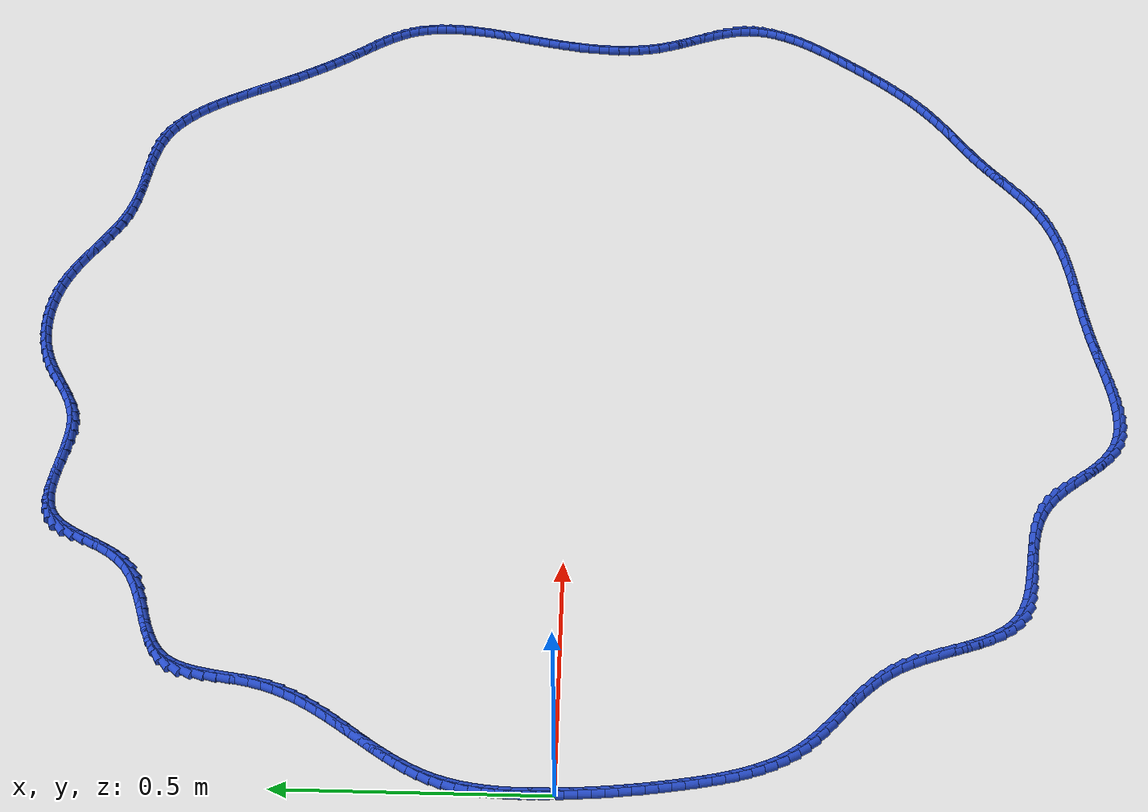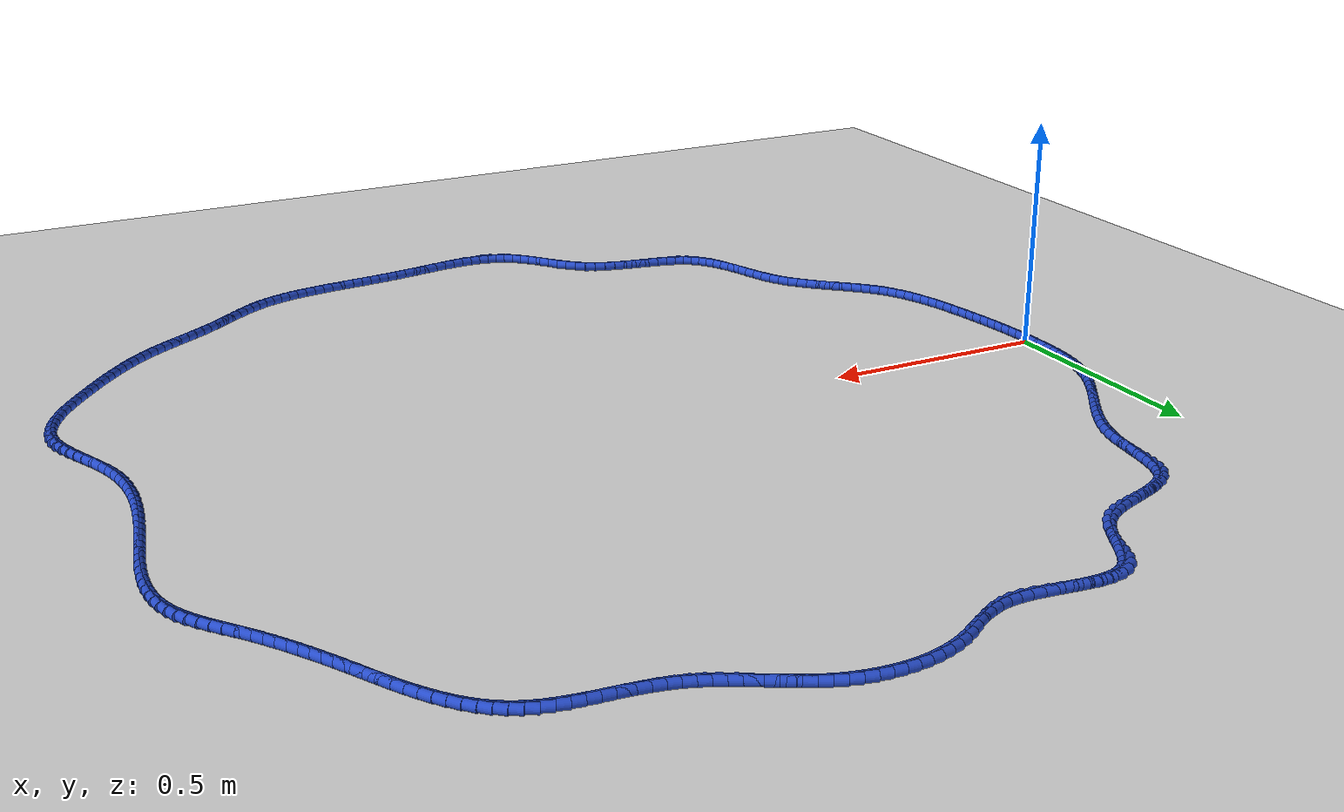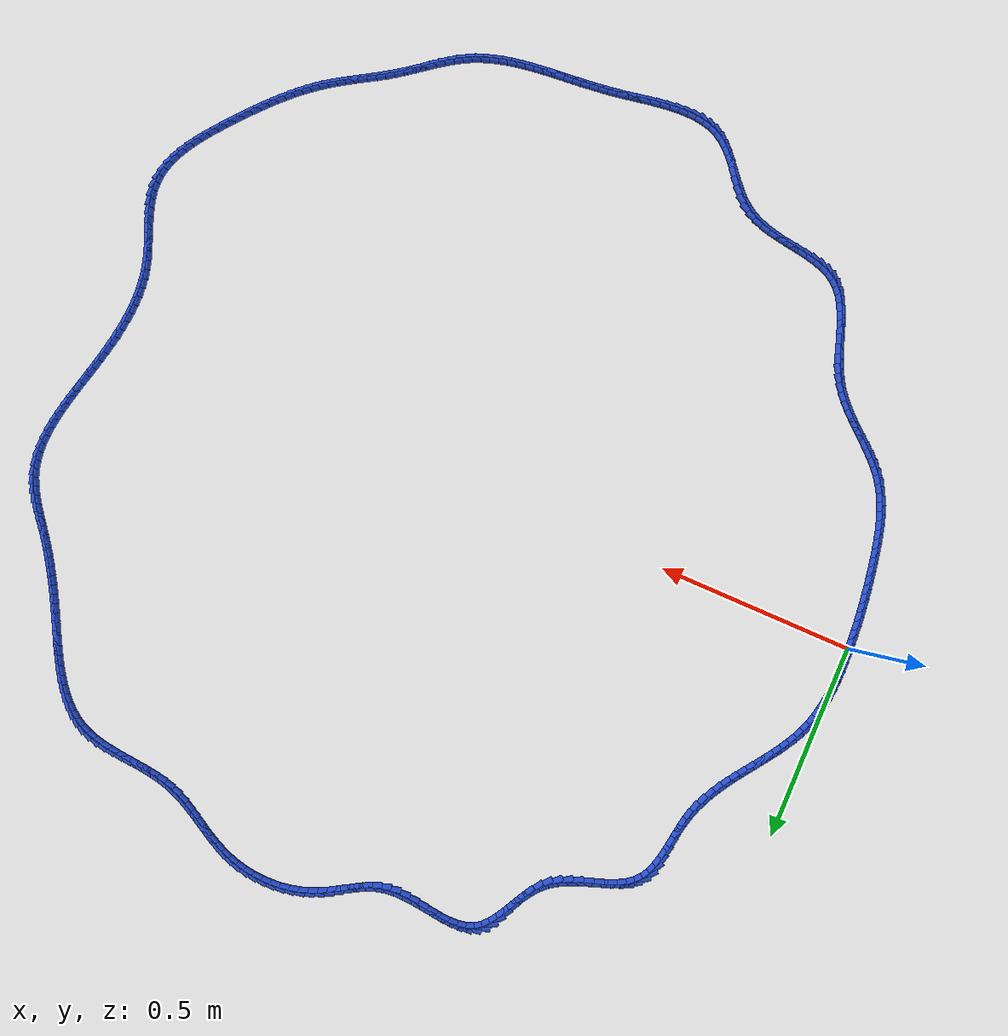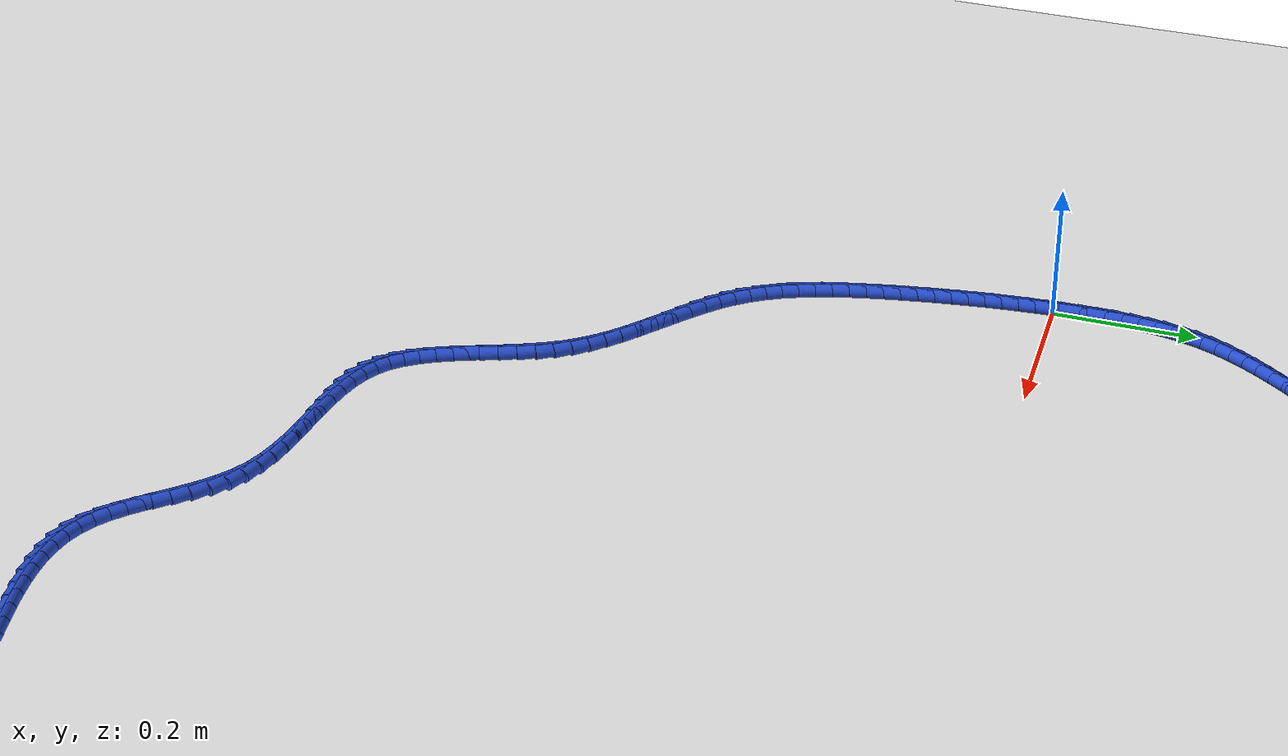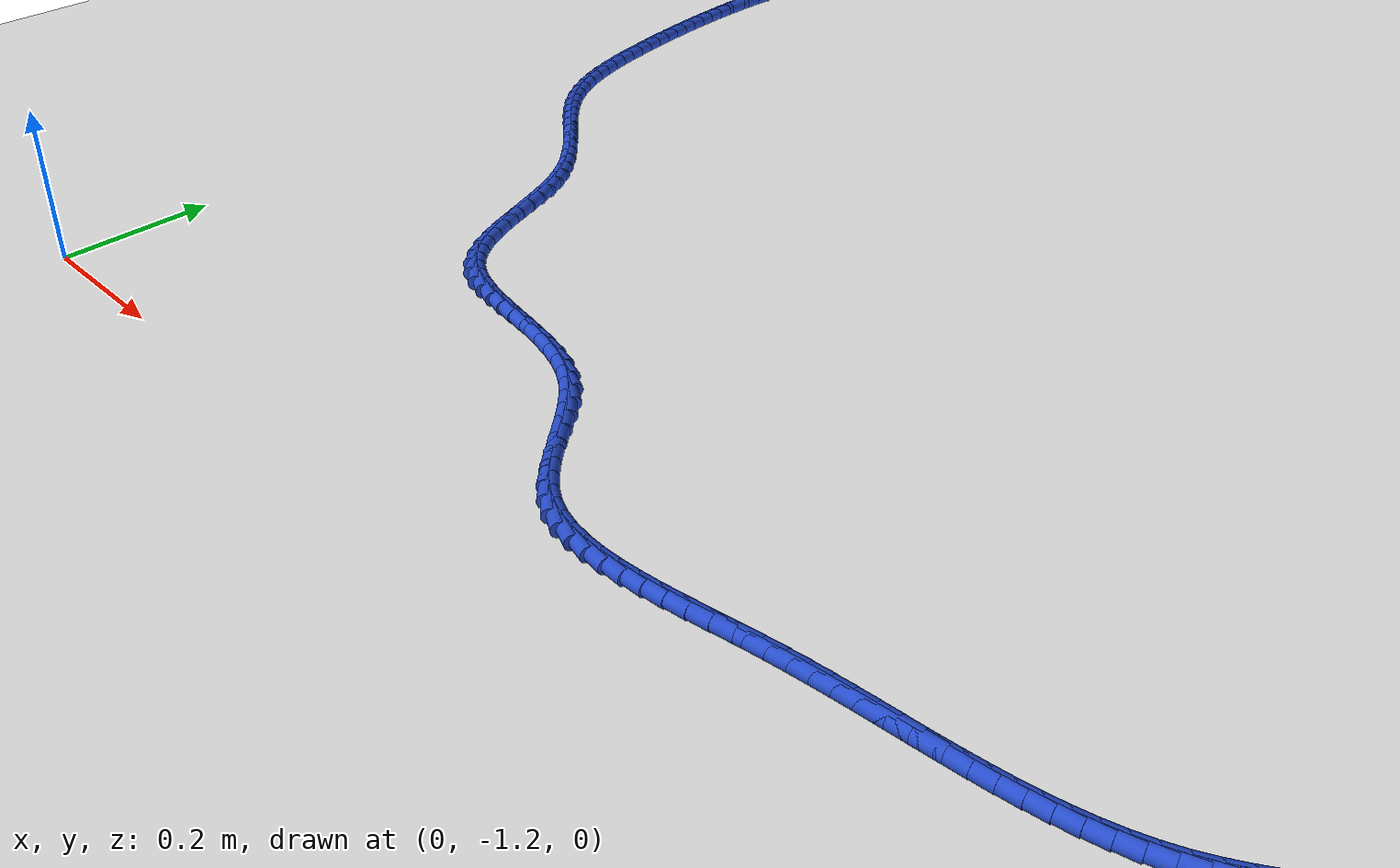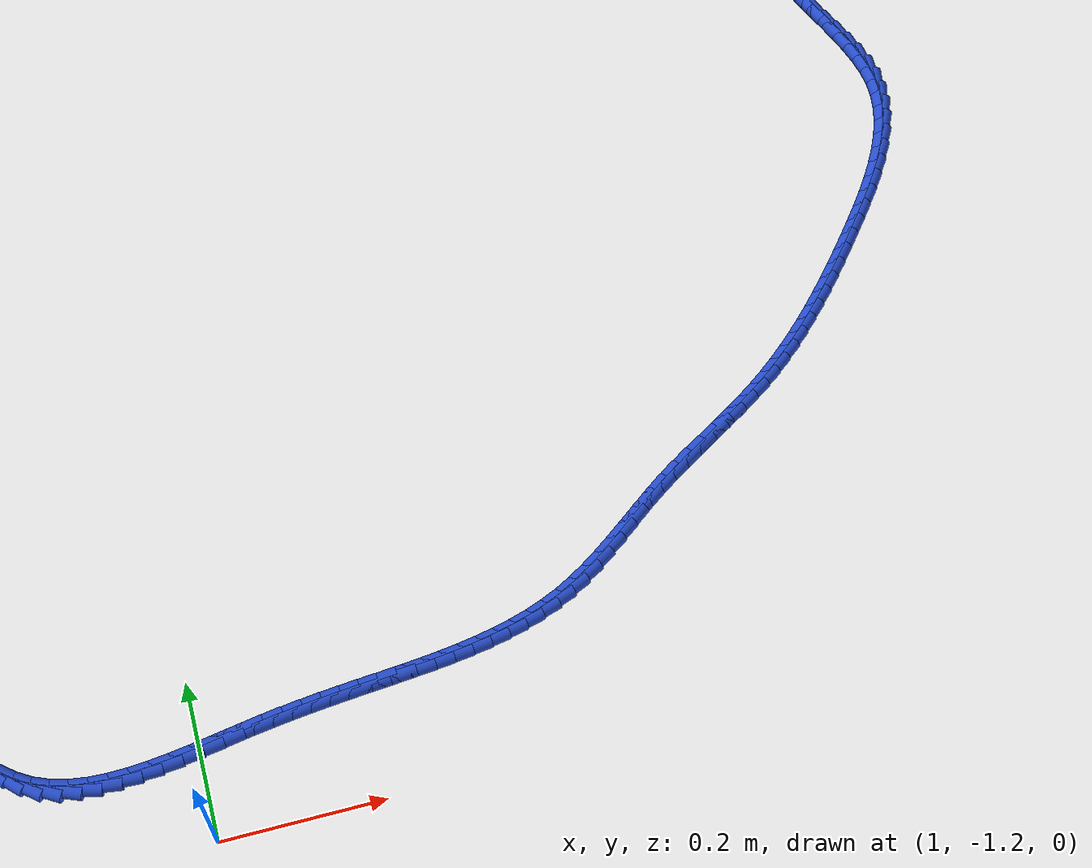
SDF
<sdf version="1.6">
 <world name="default">
  <light name="sun" type="directional">
   <pose>0 0 10 0 -0 0</pose>
   <diffuse>0.8 0.8 0.8 1</diffuse>
   <specular>0.2 0.2 0.2 1</specular>
   <attenuation>
    <range>1000</range>
    <constant>0.9</constant>
    <linear>0.01</linear>
    <quadratic>0.001</quadratic>
   </attenuation>
   <direction>-0.5 0.1 -0.9</direction>
  </light>
  <model name="ground_plane">
   <static>1</static>
   <link name="link">
    <collision name="collision">
     <geometry><plane><normal>0 0 1</normal><size>100 100</size></plane></geometry>
     <surface><friction><ode><mu>100</mu><mu2>50</mu2></ode></friction></surface>
    </collision>
    <visual name="visual">
     <cast_shadows>0</cast_shadows>
     <geometry><plane><normal>0 0 1</normal><size>100 100</size></plane></geometry>
     <material>
      <script><uri>file://media/materials/scripts/gazebo.material</uri><name>Gazebo/WhiteGlow</name></script>
     </material>
    </visual>
   </link>
  </model>
  <gravity>0 0 -9.8</gravity>
  <magnetic_field>6e-06 2.3e-05 -4.2e-05</magnetic_field>
  <atmosphere type="adiabatic"/>
  <physics name="default_physics" default="0" type="ode">
   <max_step_size>0.001</max_step_size>
   <real_time_factor>1</real_time_factor>
   <real_time_update_rate>1000</real_time_update_rate>
  </physics>
  <scene><ambient>0.4 0.4 0.4 1</ambient><background>0.7 0.7 0.7 1</background><shadows>1</shadows></scene>
  <spherical_coordinates>
   <surface_model>EARTH_WGS84</surface_model>
   <latitude_deg>0</latitude_deg>
   <longitude_deg>0</longitude_deg>
   <elevation>0</elevation>
   <heading_deg>0</heading_deg>
  </spherical_coordinates>
  <model name="line">
   <link name="link_0">
    <pose>1.8214596497756474e-17 0.0 0.01 0 1.57 -1.538473802093192</pose>
    <collision name="collision">
     <geometry><cylinder><radius>0.01</radius><length>0.08</length></cylinder></geometry>
    </collision>
    <visual name="visual">
     <material>
      <script><name>Gazebo/Blue</name><uri>file://media/materials/scripts/gazebo.material</uri></script>
     </material>
     <geometry><cylinder><radius>0.01</radius><length>0.08</length></cylinder></geometry>
    </visual>
   </link>
   <link name="link_1">
    <pose>-0.0007677014303652256 0.02374301104034909 0.01 0 1.57 -1.5591126122774837</pose>
    <collision name="collision">
     <geometry><cylinder><radius>0.01</radius><length>0.08</length></cylinder></geometry>
    </collision>
    <visual name="visual">
     <material>
      <script><name>Gazebo/Blue</name><uri>file://media/materials/scripts/gazebo.material</uri></script>
     </material>
     <geometry><cylinder><radius>0.01</radius><length>0.08</length></cylinder></geometry>
    </visual>
   </link>
   <link name="link_2">
    <pose>-0.0010465392331661615 0.04760743483264447 0.01 0 1.57 1.5566194134739137</pose>
    <collision name="collision">
     <geometry><cylinder><radius>0.01</radius><length>0.08</length></cylinder></geometry>
    </collision>
    <visual name="visual">
     <material>
      <script><name>Gazebo/Blue</name><uri>file://media/materials/scripts/gazebo.material</uri></script>
     </material>
     <geometry><cylinder><radius>0.01</radius><length>0.08</length></cylinder></geometry>
    </visual>
   </link>
   <link name="link_3">
    <pose>-0.0007078849186716965 0.07149356705283563 0.01 0 1.57 1.5252646155248755</pose>
    <collision name="collision">
     <geometry><cylinder><radius>0.01</radius><length>0.08</length></cylinder></geometry>
    </collision>
    <visual name="visual">
     <material>
      <script><name>Gazebo/Blue</name><uri>file://media/materials/scripts/gazebo.material</uri></script>
     </material>
     <geometry><cylinder><radius>0.01</radius><length>0.08</length></cylinder></geometry>
    </visual>
   </link>
   <link name="link_4">
    <pose>0.00037689000284926266 0.09530170337687202 0.01 0 1.57 1.4880618823220018</pose>
    <collision name="collision">
     <geometry><cylinder><radius>0.01</radius><length>0.08</length></cylinder></geometry>
    </collision>
    <visual name="visual">
     <material>
      <script><name>Gazebo/Blue</name><uri>file://media/materials/scripts/gazebo.material</uri></script>
     </material>
     <geometry><cylinder><radius>0.01</radius><length>0.08</length></cylinder></geometry>
    </visual>
   </link>
   <link name="link_5">
    <pose>0.002336414021127808 0.11893213948070316 0.01 0 1.57 1.4445962079937473</pose>
    <collision name="collision">
     <geometry><cylinder><radius>0.01</radius><length>0.08</length></cylinder></geometry>
    </collision>
    <visual name="visual">
     <material>
      <script><name>Gazebo/Blue</name><uri>file://media/materials/scripts/gazebo.material</uri></script>
     </material>
     <geometry><cylinder><radius>0.01</radius><length>0.08</length></cylinder></geometry>
    </visual>
   </link>
   <link name="link_6">
    <pose>0.005299315625895032 0.1422851710402786 0.01 0 1.57 1.394422207475839</pose>
    <collision name="collision">
     <geometry><cylinder><radius>0.01</radius><length>0.08</length></cylinder></geometry>
    </collision>
    <visual name="visual">
     <material>
      <script><name>Gazebo/Blue</name><uri>file://media/materials/scripts/gazebo.material</uri></script>
     </material>
     <geometry><cylinder><radius>0.01</radius><length>0.08</length></cylinder></geometry>
    </visual>
   </link>
   <link name="link_7">
    <pose>0.009394223306882029 0.16526109373154782 0.01 0 1.57 1.337111553101846</pose>
    <collision name="collision">
     <geometry><cylinder><radius>0.01</radius><length>0.08</length></cylinder></geometry>
    </collision>
    <visual name="visual">
     <material>
      <script><name>Gazebo/Blue</name><uri>file://media/materials/scripts/gazebo.material</uri></script>
     </material>
     <geometry><cylinder><radius>0.01</radius><length>0.08</length></cylinder></geometry>
    </visual>
   </link>
   <link name="link_8">
    <pose>0.014749765553819889 0.18776020323046022 0.01 0 1.57 1.272322714701313</pose>
    <collision name="collision">
     <geometry><cylinder><radius>0.01</radius><length>0.08</length></cylinder></geometry>
    </collision>
    <visual name="visual">
     <material>
      <script><name>Gazebo/Blue</name><uri>file://media/materials/scripts/gazebo.material</uri></script>
     </material>
     <geometry><cylinder><radius>0.01</radius><length>0.08</length></cylinder></geometry>
    </visual>
   </link>
   <link name="link_9">
    <pose>0.0214945708564397 0.20968279521296543 0.01 0 1.57 1.2010960972940572</pose>
    <collision name="collision">
     <geometry><cylinder><radius>0.01</radius><length>0.08</length></cylinder></geometry>
    </collision>
    <visual name="visual">
     <material>
      <script><name>Gazebo/Blue</name><uri>file://media/materials/scripts/gazebo.material</uri></script>
     </material>
     <geometry><cylinder><radius>0.01</radius><length>0.08</length></cylinder></geometry>
    </visual>
   </link>
   <link name="link_10">
    <pose>0.029733590960922738 0.23094377662411106 0.01 0 1.57 1.1340430050891197</pose>
    <collision name="collision">
     <geometry><cylinder><radius>0.01</radius><length>0.08</length></cylinder></geometry>
    </collision>
    <visual name="visual">
     <material>
      <script><name>Gazebo/Blue</name><uri>file://media/materials/scripts/gazebo.material</uri></script>
     </material>
     <geometry><cylinder><radius>0.01</radius><length>0.08</length></cylinder></geometry>
    </visual>
   </link>
   <link name="link_11">
    <pose>0.03936860333262791 0.25158343626666013 0.01 0 1.57 1.0770773024523659</pose>
    <collision name="collision">
     <geometry><cylinder><radius>0.01</radius><length>0.08</length></cylinder></geometry>
    </collision>
    <visual name="visual">
     <material>
      <script><name>Gazebo/Blue</name><uri>file://media/materials/scripts/gazebo.material</uri></script>
     </material>
     <geometry><cylinder><radius>0.01</radius><length>0.08</length></cylinder></geometry>
    </visual>
   </link>
   <link name="link_12">
    <pose>0.05019798939827478 0.2717058701701199 0.01 0 1.57 1.030547085178031</pose>
    <collision name="collision">
     <geometry><cylinder><radius>0.01</radius><length>0.08</length></cylinder></geometry>
    </collision>
    <visual name="visual">
     <material>
      <script><name>Gazebo/Blue</name><uri>file://media/materials/scripts/gazebo.material</uri></script>
     </material>
     <geometry><cylinder><radius>0.01</radius><length>0.08</length></cylinder></geometry>
    </visual>
   </link>
   <link name="link_13">
    <pose>0.06201931173426346 0.2914156796886567 0.01 0 1.57 0.9944334268146502</pose>
    <collision name="collision">
     <geometry><cylinder><radius>0.01</radius><length>0.08</length></cylinder></geometry>
    </collision>
    <visual name="visual">
     <material>
      <script><name>Gazebo/Blue</name><uri>file://media/materials/scripts/gazebo.material</uri></script>
     </material>
     <geometry><cylinder><radius>0.01</radius><length>0.08</length></cylinder></geometry>
    </visual>
   </link>
   <link name="link_14">
    <pose>0.07463013291699404 0.3108174661764372 0.01 0 1.57 0.968544111001394</pose>
    <collision name="collision">
     <geometry><cylinder><radius>0.01</radius><length>0.08</length></cylinder></geometry>
    </collision>
    <visual name="visual">
     <material>
      <script><name>Gazebo/Blue</name><uri>file://media/materials/scripts/gazebo.material</uri></script>
     </material>
     <geometry><cylinder><radius>0.01</radius><length>0.08</length></cylinder></geometry>
    </visual>
   </link>
   <link name="link_15">
    <pose>0.08782801552286672 0.33001583098762793 0.01 0 1.57 0.9526309485638088</pose>
    <collision name="collision">
     <geometry><cylinder><radius>0.01</radius><length>0.08</length></cylinder></geometry>
    </collision>
    <visual name="visual">
     <material>
      <script><name>Gazebo/Blue</name><uri>file://media/materials/scripts/gazebo.material</uri></script>
     </material>
     <geometry><cylinder><radius>0.01</radius><length>0.08</length></cylinder></geometry>
    </visual>
   </link>
   <link name="link_16">
    <pose>0.10141052212828153 0.34911537547639526 0.01 0 1.57 0.9464679651802381</pose>
    <collision name="collision">
     <geometry><cylinder><radius>0.01</radius><length>0.08</length></cylinder></geometry>
    </collision>
    <visual name="visual">
     <material>
      <script><name>Gazebo/Blue</name><uri>file://media/materials/scripts/gazebo.material</uri></script>
     </material>
     <geometry><cylinder><radius>0.01</radius><length>0.08</length></cylinder></geometry>
    </visual>
   </link>
   <link name="link_17">
    <pose>0.11517521530963862 0.36822070099690574 0.01 0 1.57 0.9498945976807526</pose>
    <collision name="collision">
     <geometry><cylinder><radius>0.01</radius><length>0.08</length></cylinder></geometry>
    </collision>
    <visual name="visual">
     <material>
      <script><name>Gazebo/Blue</name><uri>file://media/materials/scripts/gazebo.material</uri></script>
     </material>
     <geometry><cylinder><radius>0.01</radius><length>0.08</length></cylinder></geometry>
    </visual>
   </link>
   <link name="link_18">
    <pose>0.12891965764333815 0.3874364089033259 0.01 0 1.57 0.9628295716358256</pose>
    <collision name="collision">
     <geometry><cylinder><radius>0.01</radius><length>0.08</length></cylinder></geometry>
    </collision>
    <visual name="visual">
     <material>
      <script><name>Gazebo/Blue</name><uri>file://media/materials/scripts/gazebo.material</uri></script>
     </material>
     <geometry><cylinder><radius>0.01</radius><length>0.08</length></cylinder></geometry>
    </visual>
   </link>
   <link name="link_19">
    <pose>0.14244141170578012 0.4068671005498222 0.01 0 1.57 0.9852592882658145</pose>
    <collision name="collision">
     <geometry><cylinder><radius>0.01</radius><length>0.08</length></cylinder></geometry>
    </collision>
    <visual name="visual">
     <material>
      <script><name>Gazebo/Blue</name><uri>file://media/materials/scripts/gazebo.material</uri></script>
     </material>
     <geometry><cylinder><radius>0.01</radius><length>0.08</length></cylinder></geometry>
    </visual>
   </link>
   <link name="link_20">
    <pose>0.15553804007336486 0.42661737729056126 0.01 0 1.57 1.0172018359766788</pose>
    <collision name="collision">
     <geometry><cylinder><radius>0.01</radius><length>0.08</length></cylinder></geometry>
    </collision>
    <visual name="visual">
     <material>
      <script><name>Gazebo/Blue</name><uri>file://media/materials/scripts/gazebo.material</uri></script>
     </material>
     <geometry><cylinder><radius>0.01</radius><length>0.08</length></cylinder></geometry>
    </visual>
   </link>
   <link name="link_21">
    <pose>0.16800710532249227 0.4467918404797094 0.01 0 1.57 1.0586459094893708</pose>
    <collision name="collision">
     <geometry><cylinder><radius>0.01</radius><length>0.08</length></cylinder></geometry>
    </collision>
    <visual name="visual">
     <material>
      <script><name>Gazebo/Blue</name><uri>file://media/materials/scripts/gazebo.material</uri></script>
     </material>
     <geometry><cylinder><radius>0.01</radius><length>0.08</length></cylinder></geometry>
    </visual>
   </link>
   <link name="link_22">
    <pose>0.1796461700295625 0.4674950914714331 0.01 0 1.57 1.1094645334912947</pose>
    <collision name="collision">
     <geometry><cylinder><radius>0.01</radius><length>0.08</length></cylinder></geometry>
    </collision>
    <visual name="visual">
     <material>
      <script><name>Gazebo/Blue</name><uri>file://media/materials/scripts/gazebo.material</uri></script>
     </material>
     <geometry><cylinder><radius>0.01</radius><length>0.08</length></cylinder></geometry>
    </visual>
   </link>
   <link name="link_23">
    <pose>0.19025279677097579 0.488831731619899 0.01 0 1.57 1.1693081653867587</pose>
    <collision name="collision">
     <geometry><cylinder><radius>0.01</radius><length>0.08</length></cylinder></geometry>
    </collision>
    <visual name="visual">
     <material>
      <script><name>Gazebo/Blue</name><uri>file://media/materials/scripts/gazebo.material</uri></script>
     </material>
     <geometry><cylinder><radius>0.01</radius><length>0.08</length></cylinder></geometry>
    </visual>
   </link>
   <link name="link_24">
    <pose>0.19962454812313224 0.5109063622792738 0.01 0 1.57 1.237491480410047</pose>
    <collision name="collision">
     <geometry><cylinder><radius>0.01</radius><length>0.08</length></cylinder></geometry>
    </collision>
    <visual name="visual">
     <material>
      <script><name>Gazebo/Blue</name><uri>file://media/materials/scripts/gazebo.material</uri></script>
     </material>
     <geometry><cylinder><radius>0.01</radius><length>0.08</length></cylinder></geometry>
    </visual>
   </link>
   <link name="link_25">
    <pose>0.2075589866624319 0.5338235848037236 0.01 0 1.57 1.3121350676280372</pose>
    <collision name="collision">
     <geometry><cylinder><radius>0.01</radius><length>0.08</length></cylinder></geometry>
    </collision>
    <visual name="visual">
     <material>
      <script><name>Gazebo/Blue</name><uri>file://media/materials/scripts/gazebo.material</uri></script>
     </material>
     <geometry><cylinder><radius>0.01</radius><length>0.08</length></cylinder></geometry>
    </visual>
   </link>
   <link name="link_26">
    <pose>0.21387014389067138 0.557676305284221 0.01 0 1.57 1.3735472927225385</pose>
    <collision name="collision">
     <geometry><cylinder><radius>0.01</radius><length>0.08</length></cylinder></geometry>
    </collision>
    <visual name="visual">
     <material>
      <script><name>Gazebo/Blue</name><uri>file://media/materials/scripts/gazebo.material</uri></script>
     </material>
     <geometry><cylinder><radius>0.01</radius><length>0.08</length></cylinder></geometry>
    </visual>
   </link>
   <link name="link_27">
    <pose>0.21878409946325075 0.582264817422709 0.01 0 1.57 1.4041628358587832</pose>
    <collision name="collision">
     <geometry><cylinder><radius>0.01</radius><length>0.08</length></cylinder></geometry>
    </collision>
    <visual name="visual">
     <material>
      <script><name>Gazebo/Blue</name><uri>file://media/materials/scripts/gazebo.material</uri></script>
     </material>
     <geometry><cylinder><radius>0.01</radius><length>0.08</length></cylinder></geometry>
    </visual>
   </link>
   <link name="link_28">
    <pose>0.222958354186704 0.6070830449675048 0.01 0 1.57 1.4046760108720817</pose>
    <collision name="collision">
     <geometry><cylinder><radius>0.01</radius><length>0.08</length></cylinder></geometry>
    </collision>
    <visual name="visual">
     <material>
      <script><name>Gazebo/Blue</name><uri>file://media/materials/scripts/gazebo.material</uri></script>
     </material>
     <geometry><cylinder><radius>0.01</radius><length>0.08</length></cylinder></geometry>
    </visual>
   </link>
   <link name="link_29">
    <pose>0.22707075495657741 0.6316104630699318 0.01 0 1.57 1.3740018208485782</pose>
    <collision name="collision">
     <geometry><cylinder><radius>0.01</radius><length>0.08</length></cylinder></geometry>
    </collision>
    <visual name="visual">
     <material>
      <script><name>Gazebo/Blue</name><uri>file://media/materials/scripts/gazebo.material</uri></script>
     </material>
     <geometry><cylinder><radius>0.01</radius><length>0.08</length></cylinder></geometry>
    </visual>
   </link>
   <link name="link_30">
    <pose>0.23179914866841714 0.6553265468813139 0.01 0 1.57 1.3079802400317275</pose>
    <collision name="collision">
     <geometry><cylinder><radius>0.01</radius><length>0.08</length></cylinder></geometry>
    </collision>
    <visual name="visual">
     <material>
      <script><name>Gazebo/Blue</name><uri>file://media/materials/scripts/gazebo.material</uri></script>
     </material>
     <geometry><cylinder><radius>0.01</radius><length>0.08</length></cylinder></geometry>
    </visual>
   </link>
   <link name="link_31">
    <pose>0.23782138221776936 0.6777107715529743 0.01 0 1.57 1.1995109880548842</pose>
    <collision name="collision">
     <geometry><cylinder><radius>0.01</radius><length>0.08</length></cylinder></geometry>
    </collision>
    <visual name="visual">
     <material>
      <script><name>Gazebo/Blue</name><uri>file://media/materials/scripts/gazebo.material</uri></script>
     </material>
     <geometry><cylinder><radius>0.01</radius><length>0.08</length></cylinder></geometry>
    </visual>
   </link>
   <link name="link_32">
    <pose>0.2458153025001804 0.6982426122362374 0.01 0 1.57 1.0406394588289851</pose>
    <collision name="collision">
     <geometry><cylinder><radius>0.01</radius><length>0.08</length></cylinder></geometry>
    </collision>
    <visual name="visual">
     <material>
      <script><name>Gazebo/Blue</name><uri>file://media/materials/scripts/gazebo.material</uri></script>
     </material>
     <geometry><cylinder><radius>0.01</radius><length>0.08</length></cylinder></geometry>
    </visual>
   </link>
   <link name="link_33">
    <pose>0.2564587564111964 0.7164015440824264 0.01 0 1.57 0.8342582517688095</pose>
    <collision name="collision">
     <geometry><cylinder><radius>0.01</radius><length>0.08</length></cylinder></geometry>
    </collision>
    <visual name="visual">
     <material>
      <script><name>Gazebo/Blue</name><uri>file://media/materials/scripts/gazebo.material</uri></script>
     </material>
     <geometry><cylinder><radius>0.01</radius><length>0.08</length></cylinder></geometry>
    </visual>
   </link>
   <link name="link_34">
    <pose>0.2703579488856261 0.7317299364286659 0.01 0 1.57 0.6416369942503576</pose>
    <collision name="collision">
     <geometry><cylinder><radius>0.01</radius><length>0.08</length></cylinder></geometry>
    </collision>
    <visual name="visual">
     <material>
      <script><name>Gazebo/Blue</name><uri>file://media/materials/scripts/gazebo.material</uri></script>
     </material>
     <geometry><cylinder><radius>0.01</radius><length>0.08</length></cylinder></geometry>
    </visual>
   </link>
   <link name="link_35">
    <pose>0.2873627900470792 0.7444341067492681 0.01 0 1.57 0.5011155887924594</pose>
    <collision name="collision">
     <geometry><cylinder><radius>0.01</radius><length>0.08</length></cylinder></geometry>
    </collision>
    <visual name="visual">
     <material>
      <script><name>Gazebo/Blue</name><uri>file://media/materials/scripts/gazebo.material</uri></script>
     </material>
     <geometry><cylinder><radius>0.01</radius><length>0.08</length></cylinder></geometry>
    </visual>
   </link>
   <link name="link_36">
    <pose>0.3068693041826186 0.7551188370474655 0.01 0 1.57 0.4090261510488583</pose>
    <collision name="collision">
     <geometry><cylinder><radius>0.01</radius><length>0.08</length></cylinder></geometry>
    </collision>
    <visual name="visual">
     <material>
      <script><name>Gazebo/Blue</name><uri>file://media/materials/scripts/gazebo.material</uri></script>
     </material>
     <geometry><cylinder><radius>0.01</radius><length>0.08</length></cylinder></geometry>
    </visual>
   </link>
   <link name="link_37">
    <pose>0.32826734317652434 0.764394328053778 0.01 0 1.57 0.35767513498691905</pose>
    <collision name="collision">
     <geometry><cylinder><radius>0.01</radius><length>0.08</length></cylinder></geometry>
    </collision>
    <visual name="visual">
     <material>
      <script><name>Gazebo/Blue</name><uri>file://media/materials/scripts/gazebo.material</uri></script>
     </material>
     <geometry><cylinder><radius>0.01</radius><length>0.08</length></cylinder></geometry>
    </visual>
   </link>
   <link name="link_38">
    <pose>0.3509467589130762 0.7728707804987246 0.01 0 1.57 0.34105130024242375</pose>
    <collision name="collision">
     <geometry><cylinder><radius>0.01</radius><length>0.08</length></cylinder></geometry>
    </collision>
    <visual name="visual">
     <material>
      <script><name>Gazebo/Blue</name><uri>file://media/materials/scripts/gazebo.material</uri></script>
     </material>
     <geometry><cylinder><radius>0.01</radius><length>0.08</length></cylinder></geometry>
    </visual>
   </link>
   <link name="link_39">
    <pose>0.37429740327655453 0.7811583951128248 0.01 0 1.57 0.3561310335240268</pose>
    <collision name="collision">
     <geometry><cylinder><radius>0.01</radius><length>0.08</length></cylinder></geometry>
    </collision>
    <visual name="visual">
     <material>
      <script><name>Gazebo/Blue</name><uri>file://media/materials/scripts/gazebo.material</uri></script>
     </material>
     <geometry><cylinder><radius>0.01</radius><length>0.08</length></cylinder></geometry>
    </visual>
   </link>
   <link name="link_40">
    <pose>0.39770912815123916 0.7898673726265978 0.01 0 1.57 0.4027561912875621</pose>
    <collision name="collision">
     <geometry><cylinder><radius>0.01</radius><length>0.08</length></cylinder></geometry>
    </collision>
    <visual name="visual">
     <material>
      <script><name>Gazebo/Blue</name><uri>file://media/materials/scripts/gazebo.material</uri></script>
     </material>
     <geometry><cylinder><radius>0.01</radius><length>0.08</length></cylinder></geometry>
    </visual>
   </link>
   <link name="link_41">
    <pose>0.42057178542140966 0.7996079137705627 0.01 0 1.57 0.48301341500667005</pose>
    <collision name="collision">
     <geometry><cylinder><radius>0.01</radius><length>0.08</length></cylinder></geometry>
    </collision>
    <visual name="visual">
     <material>
      <script><name>Gazebo/Blue</name><uri>file://media/materials/scripts/gazebo.material</uri></script>
     </material>
     <geometry><cylinder><radius>0.01</radius><length>0.08</length></cylinder></geometry>
    </visual>
   </link>
   <link name="link_42">
    <pose>0.4422752269713467 0.8109902192752396 0.01 0 1.57 0.5998849793796706</pose>
    <collision name="collision">
     <geometry><cylinder><radius>0.01</radius><length>0.08</length></cylinder></geometry>
    </collision>
    <visual name="visual">
     <material>
      <script><name>Gazebo/Blue</name><uri>file://media/materials/scripts/gazebo.material</uri></script>
     </material>
     <geometry><cylinder><radius>0.01</radius><length>0.08</length></cylinder></geometry>
    </visual>
   </link>
   <link name="link_43">
    <pose>0.4622093046853295 0.824624489871147 0.01 0 1.57 0.753157286381255</pose>
    <collision name="collision">
     <geometry><cylinder><radius>0.01</radius><length>0.08</length></cylinder></geometry>
    </collision>
    <visual name="visual">
     <material>
      <script><name>Gazebo/Blue</name><uri>file://media/materials/scripts/gazebo.material</uri></script>
     </material>
     <geometry><cylinder><radius>0.01</radius><length>0.08</length></cylinder></geometry>
    </visual>
   </link>
   <link name="link_44">
    <pose>0.4797816181430708 0.841098732018193 0.01 0 1.57 0.9020097063208894</pose>
    <collision name="collision">
     <geometry><cylinder><radius>0.01</radius><length>0.08</length></cylinder></geometry>
    </collision>
    <visual name="visual">
     <material>
      <script><name>Gazebo/Blue</name><uri>file://media/materials/scripts/gazebo.material</uri></script>
     </material>
     <geometry><cylinder><radius>0.01</radius><length>0.08</length></cylinder></geometry>
    </visual>
   </link>
   <link name="link_45">
    <pose>0.4949581384266521 0.8603026841519736 0.01 0 1.57 1.0027330679841202</pose>
    <collision name="collision">
     <geometry><cylinder><radius>0.01</radius><length>0.08</length></cylinder></geometry>
    </collision>
    <visual name="visual">
     <material>
      <script><name>Gazebo/Blue</name><uri>file://media/materials/scripts/gazebo.material</uri></script>
     </material>
     <geometry><cylinder><radius>0.01</radius><length>0.08</length></cylinder></geometry>
    </visual>
   </link>
   <link name="link_46">
    <pose>0.5083621012835805 0.8813041464511573 0.01 0 1.57 1.0577530732883769</pose>
    <collision name="collision">
     <geometry><cylinder><radius>0.01</radius><length>0.08</length></cylinder></geometry>
    </collision>
    <visual name="visual">
     <material>
      <script><name>Gazebo/Blue</name><uri>file://media/materials/scripts/gazebo.material</uri></script>
     </material>
     <geometry><cylinder><radius>0.01</radius><length>0.08</length></cylinder></geometry>
    </visual>
   </link>
   <link name="link_47">
    <pose>0.5206544337934746 0.9031237844324613 0.01 0 1.57 1.070456868649862</pose>
    <collision name="collision">
     <geometry><cylinder><radius>0.01</radius><length>0.08</length></cylinder></geometry>
    </collision>
    <visual name="visual">
     <material>
      <script><name>Gazebo/Blue</name><uri>file://media/materials/scripts/gazebo.material</uri></script>
     </material>
     <geometry><cylinder><radius>0.01</radius><length>0.08</length></cylinder></geometry>
    </visual>
   </link>
   <link name="link_48">
    <pose>0.5324960630359525 0.9247822636126031 0.01 0 1.57 1.0397079755922947</pose>
    <collision name="collision">
     <geometry><cylinder><radius>0.01</radius><length>0.08</length></cylinder></geometry>
    </collision>
    <visual name="visual">
     <material>
      <script><name>Gazebo/Blue</name><uri>file://media/materials/scripts/gazebo.material</uri></script>
     </material>
     <geometry><cylinder><radius>0.01</radius><length>0.08</length></cylinder></geometry>
    </visual>
   </link>
   <link name="link_49">
    <pose>0.5445479160906332 0.9453002495083006 0.01 0 1.57 0.9584564286713815</pose>
    <collision name="collision">
     <geometry><cylinder><radius>0.01</radius><length>0.08</length></cylinder></geometry>
    </collision>
    <visual name="visual">
     <material>
      <script><name>Gazebo/Blue</name><uri>file://media/materials/scripts/gazebo.material</uri></script>
     </material>
     <geometry><cylinder><radius>0.01</radius><length>0.08</length></cylinder></geometry>
    </visual>
   </link>
   <link name="link_50">
    <pose>0.5574709200371347 0.9636984076362707 0.01 0 1.57 0.8137535295504066</pose>
    <collision name="collision">
     <geometry><cylinder><radius>0.01</radius><length>0.08</length></cylinder></geometry>
    </collision>
    <visual name="visual">
     <material>
      <script><name>Gazebo/Blue</name><uri>file://media/materials/scripts/gazebo.material</uri></script>
     </material>
     <geometry><cylinder><radius>0.01</radius><length>0.08</length></cylinder></geometry>
    </visual>
   </link>
   <link name="link_51">
    <pose>0.5719260019550757 0.9789974035132312 0.01 0 1.57 0.5944971484550092</pose>
    <collision name="collision">
     <geometry><cylinder><radius>0.01</radius><length>0.08</length></cylinder></geometry>
    </collision>
    <visual name="visual">
     <material>
      <script><name>Gazebo/Blue</name><uri>file://media/materials/scripts/gazebo.material</uri></script>
     </material>
     <geometry><cylinder><radius>0.01</radius><length>0.08</length></cylinder></geometry>
    </visual>
   </link>
   <link name="link_52">
    <pose>0.5885592325579937 0.9902429411478045 0.01 0 1.57 0.35333270556785445</pose>
    <collision name="collision">
     <geometry><cylinder><radius>0.01</radius><length>0.08</length></cylinder></geometry>
    </collision>
    <visual name="visual">
     <material>
      <script><name>Gazebo/Blue</name><uri>file://media/materials/scripts/gazebo.material</uri></script>
     </material>
     <geometry><cylinder><radius>0.01</radius><length>0.08</length></cylinder></geometry>
    </visual>
   </link>
   <link name="link_53">
    <pose>0.6075598988486609 0.9972505746709178 0.01 0 1.57 0.16408694424527606</pose>
    <collision name="collision">
     <geometry><cylinder><radius>0.01</radius><length>0.08</length></cylinder></geometry>
    </collision>
    <visual name="visual">
     <material>
      <script><name>Gazebo/Blue</name><uri>file://media/materials/scripts/gazebo.material</uri></script>
     </material>
     <geometry><cylinder><radius>0.01</radius><length>0.08</length></cylinder></geometry>
    </visual>
   </link>
   <link name="link_54">
    <pose>0.6285856168144167 1.0007319212442285 0.01 0 1.57 0.031611582251225956</pose>
    <collision name="collision">
     <geometry><cylinder><radius>0.01</radius><length>0.08</length></cylinder></geometry>
    </collision>
    <visual name="visual">
     <material>
      <script><name>Gazebo/Blue</name><uri>file://media/materials/scripts/gazebo.material</uri></script>
     </material>
     <geometry><cylinder><radius>0.01</radius><length>0.08</length></cylinder></geometry>
    </visual>
   </link>
   <link name="link_55">
    <pose>0.6512640603207688 1.0014490616199532 0.01 0 1.57 -0.053581682121296104</pose>
    <collision name="collision">
     <geometry><cylinder><radius>0.01</radius><length>0.08</length></cylinder></geometry>
    </collision>
    <visual name="visual">
     <material>
      <script><name>Gazebo/Blue</name><uri>file://media/materials/scripts/gazebo.material</uri></script>
     </material>
     <geometry><cylinder><radius>0.01</radius><length>0.08</length></cylinder></geometry>
    </visual>
   </link>
   <link name="link_56">
    <pose>0.6752229032332245 1.000164076550309 0.01 0 1.57 -0.10119488661212647</pose>
    <collision name="collision">
     <geometry><cylinder><radius>0.01</radius><length>0.08</length></cylinder></geometry>
    </collision>
    <visual name="visual">
     <material>
      <script><name>Gazebo/Blue</name><uri>file://media/materials/scripts/gazebo.material</uri></script>
     </material>
     <geometry><cylinder><radius>0.01</radius><length>0.08</length></cylinder></geometry>
    </visual>
   </link>
   <link name="link_57">
    <pose>0.7000898194172918 0.9976390467875128 0.01 0 1.57 -0.11766958866068457</pose>
    <collision name="collision">
     <geometry><cylinder><radius>0.01</radius><length>0.08</length></cylinder></geometry>
    </collision>
    <visual name="visual">
     <material>
      <script><name>Gazebo/Blue</name><uri>file://media/materials/scripts/gazebo.material</uri></script>
     </material>
     <geometry><cylinder><radius>0.01</radius><length>0.08</length></cylinder></geometry>
    </visual>
   </link>
   <link name="link_58">
    <pose>0.7254924827384778 0.9946360530837816 0.01 0 1.57 -0.10594880198109499</pose>
    <collision name="collision">
     <geometry><cylinder><radius>0.01</radius><length>0.08</length></cylinder></geometry>
    </collision>
    <visual name="visual">
     <material>
      <script><name>Gazebo/Blue</name><uri>file://media/materials/scripts/gazebo.material</uri></script>
     </material>
     <geometry><cylinder><radius>0.01</radius><length>0.08</length></cylinder></geometry>
    </visual>
   </link>
   <link name="link_59">
    <pose>0.7510585670622897 0.9919171761913317 0.01 0 1.57 -0.06586929468810789</pose>
    <collision name="collision">
     <geometry><cylinder><radius>0.01</radius><length>0.08</length></cylinder></geometry>
    </collision>
    <visual name="visual">
     <material>
      <script><name>Gazebo/Blue</name><uri>file://media/materials/scripts/gazebo.material</uri></script>
     </material>
     <geometry><cylinder><radius>0.01</radius><length>0.08</length></cylinder></geometry>
    </visual>
   </link>
   <link name="link_60">
    <pose>0.7764157462542358 0.9902444968623805 0.01 0 1.57 0.005472954386778778</pose>
    <collision name="collision">
     <geometry><cylinder><radius>0.01</radius><length>0.08</length></cylinder></geometry>
    </collision>
    <visual name="visual">
     <material>
      <script><name>Gazebo/Blue</name><uri>file://media/materials/scripts/gazebo.material</uri></script>
     </material>
     <geometry><cylinder><radius>0.01</radius><length>0.08</length></cylinder></geometry>
    </visual>
   </link>
   <link name="link_61">
    <pose>0.8011916941798235 0.990380095849145 0.01 0 1.57 0.11310407802574506</pose>
    <collision name="collision">
     <geometry><cylinder><radius>0.01</radius><length>0.08</length></cylinder></geometry>
    </collision>
    <visual name="visual">
     <material>
      <script><name>Gazebo/Blue</name><uri>file://media/materials/scripts/gazebo.material</uri></script>
     </material>
     <geometry><cylinder><radius>0.01</radius><length>0.08</length></cylinder></geometry>
    </visual>
   </link>
   <link name="link_62">
    <pose>0.8250140847045598 0.9930860539038417 0.01 0 1.57 0.25232088774216166</pose>
    <collision name="collision">
     <geometry><cylinder><radius>0.01</radius><length>0.08</length></cylinder></geometry>
    </collision>
    <visual name="visual">
     <material>
      <script><name>Gazebo/Blue</name><uri>file://media/materials/scripts/gazebo.material</uri></script>
     </material>
     <geometry><cylinder><radius>0.01</radius><length>0.08</length></cylinder></geometry>
    </visual>
   </link>
   <link name="link_63">
    <pose>0.8476087252554636 0.9989113047158134 0.01 0 1.57 0.375611249669344</pose>
    <collision name="collision">
     <geometry><cylinder><radius>0.01</radius><length>0.08</length></cylinder></geometry>
    </collision>
    <visual name="visual">
     <material>
      <script><name>Gazebo/Blue</name><uri>file://media/materials/scripts/gazebo.material</uri></script>
     </material>
     <geometry><cylinder><radius>0.01</radius><length>0.08</length></cylinder></geometry>
    </visual>
   </link>
   <link name="link_64">
    <pose>0.8691596382474084 1.0074095345042915 0.01 0 1.57 0.46450104938704084</pose>
    <collision name="collision">
     <geometry><cylinder><radius>0.01</radius><length>0.08</length></cylinder></geometry>
    </collision>
    <visual name="visual">
     <material>
      <script><name>Gazebo/Blue</name><uri>file://media/materials/scripts/gazebo.material</uri></script>
     </material>
     <geometry><cylinder><radius>0.01</radius><length>0.08</length></cylinder></geometry>
    </visual>
   </link>
   <link name="link_65">
    <pose>0.8899844779458053 1.0178441797919737 0.01 0 1.57 0.5179611077099553</pose>
    <collision name="collision">
     <geometry><cylinder><radius>0.01</radius><length>0.08</length></cylinder></geometry>
    </collision>
    <visual name="visual">
     <material>
      <script><name>Gazebo/Blue</name><uri>file://media/materials/scripts/gazebo.material</uri></script>
     </material>
     <geometry><cylinder><radius>0.01</radius><length>0.08</length></cylinder></geometry>
    </visual>
   </link>
   <link name="link_66">
    <pose>0.9104009143171535 1.029478642998636 0.01 0 1.57 0.5368762598951242</pose>
    <collision name="collision">
     <geometry><cylinder><radius>0.01</radius><length>0.08</length></cylinder></geometry>
    </collision>
    <visual name="visual">
     <material>
      <script><name>Gazebo/Blue</name><uri>file://media/materials/scripts/gazebo.material</uri></script>
     </material>
     <geometry><cylinder><radius>0.01</radius><length>0.08</length></cylinder></geometry>
    </visual>
   </link>
   <link name="link_67">
    <pose>0.9307266173279529 1.0415763265440552 0.01 0 1.57 0.5220733342183242</pose>
    <collision name="collision">
     <geometry><cylinder><radius>0.01</radius><length>0.08</length></cylinder></geometry>
    </collision>
    <visual name="visual">
     <material>
      <script><name>Gazebo/Blue</name><uri>file://media/materials/scripts/gazebo.material</uri></script>
     </material>
     <geometry><cylinder><radius>0.01</radius><length>0.08</length></cylinder></geometry>
    </visual>
   </link>
   <link name="link_68">
    <pose>0.9512792569447036 1.0534006328480086 0.01 0 1.57 0.47367233573308287</pose>
    <collision name="collision">
     <geometry><cylinder><radius>0.01</radius><length>0.08</length></cylinder></geometry>
    </collision>
    <visual name="visual">
     <material>
      <script><name>Gazebo/Blue</name><uri>file://media/materials/scripts/gazebo.material</uri></script>
     </material>
     <geometry><cylinder><radius>0.01</radius><length>0.08</length></cylinder></geometry>
    </visual>
   </link>
   <link name="link_69">
    <pose>0.9723765031339049 1.0642149643302712 0.01 0 1.57 0.3953165295886112</pose>
    <collision name="collision">
     <geometry><cylinder><radius>0.01</radius><length>0.08</length></cylinder></geometry>
    </collision>
    <visual name="visual">
     <material>
      <script><name>Gazebo/Blue</name><uri>file://media/materials/scripts/gazebo.material</uri></script>
     </material>
     <geometry><cylinder><radius>0.01</radius><length>0.08</length></cylinder></geometry>
    </visual>
   </link>
   <link name="link_70">
    <pose>0.9942877302964807 1.073358156326137 0.01 0 1.57 0.31134802528914113</pose>
    <collision name="collision">
     <geometry><cylinder><radius>0.01</radius><length>0.08</length></cylinder></geometry>
    </collision>
    <visual name="visual">
     <material>
      <script><name>Gazebo/Blue</name><uri>file://media/materials/scripts/gazebo.material</uri></script>
     </material>
     <geometry><cylinder><radius>0.01</radius><length>0.08</length></cylinder></geometry>
    </visual>
   </link>
   <link name="link_71">
    <pose>1.0169695787998232 1.0806575039217872 0.01 0 1.57 0.23103541337111888</pose>
    <collision name="collision">
     <geometry><cylinder><radius>0.01</radius><length>0.08</length></cylinder></geometry>
    </collision>
    <visual name="visual">
     <material>
      <script><name>Gazebo/Blue</name><uri>file://media/materials/scripts/gazebo.material</uri></script>
     </material>
     <geometry><cylinder><radius>0.01</radius><length>0.08</length></cylinder></geometry>
    </visual>
   </link>
   <link name="link_72">
    <pose>1.0402541227817694 1.0861348623821294 0.01 0 1.57 0.153829096978689</pose>
    <collision name="collision">
     <geometry><cylinder><radius>0.01</radius><length>0.08</length></cylinder></geometry>
    </collision>
    <visual name="visual">
     <material>
      <script><name>Gazebo/Blue</name><uri>file://media/materials/scripts/gazebo.material</uri></script>
     </material>
     <geometry><cylinder><radius>0.01</radius><length>0.08</length></cylinder></geometry>
    </visual>
   </link>
   <link name="link_73">
    <pose>1.0639731152185534 1.0898125885948566 0.01 0 1.57 0.07906914227122919</pose>
    <collision name="collision">
     <geometry><cylinder><radius>0.01</radius><length>0.08</length></cylinder></geometry>
    </collision>
    <visual name="visual">
     <material>
      <script><name>Gazebo/Blue</name><uri>file://media/materials/scripts/gazebo.material</uri></script>
     </material>
     <geometry><cylinder><radius>0.01</radius><length>0.08</length></cylinder></geometry>
    </visual>
   </link>
   <link name="link_74">
    <pose>1.0879583090864084 1.0917130394476604 0.01 0 1.57 0.006042839893319099</pose>
    <collision name="collision">
     <geometry><cylinder><radius>0.01</radius><length>0.08</length></cylinder></geometry>
    </collision>
    <visual name="visual">
     <material>
      <script><name>Gazebo/Blue</name><uri>file://media/materials/scripts/gazebo.material</uri></script>
     </material>
     <geometry><cylinder><radius>0.01</radius><length>0.08</length></cylinder></geometry>
    </visual>
   </link>
   <link name="link_75">
    <pose>1.1120414573615685 1.0918585718282345 0.01 0 1.57 -0.06599483840006072</pose>
    <collision name="collision">
     <geometry><cylinder><radius>0.01</radius><length>0.08</length></cylinder></geometry>
    </collision>
    <visual name="visual">
     <material>
      <script><name>Gazebo/Blue</name><uri>file://media/materials/scripts/gazebo.material</uri></script>
     </material>
     <geometry><cylinder><radius>0.01</radius><length>0.08</length></cylinder></geometry>
    </visual>
   </link>
   <link name="link_76">
    <pose>1.1360543130202665 1.090271542624271 0.01 0 1.57 -0.13780982099156985</pose>
    <collision name="collision">
     <geometry><cylinder><radius>0.01</radius><length>0.08</length></cylinder></geometry>
    </collision>
    <visual name="visual">
     <material>
      <script><name>Gazebo/Blue</name><uri>file://media/materials/scripts/gazebo.material</uri></script>
     </material>
     <geometry><cylinder><radius>0.01</radius><length>0.08</length></cylinder></geometry>
    </visual>
   </link>
   <link name="link_77">
    <pose>1.159828629038737 1.086974308723462 0.01 0 1.57 -0.2101829460826411</pose>
    <collision name="collision">
     <geometry><cylinder><radius>0.01</radius><length>0.08</length></cylinder></geometry>
    </collision>
    <visual name="visual">
     <material>
      <script><name>Gazebo/Blue</name><uri>file://media/materials/scripts/gazebo.material</uri></script>
     </material>
     <geometry><cylinder><radius>0.01</radius><length>0.08</length></cylinder></geometry>
    </visual>
   </link>
   <link name="link_78">
    <pose>1.183196158393214 1.0819892270135005 0.01 0 1.57 -0.2839057608263204</pose>
    <collision name="collision">
     <geometry><cylinder><radius>0.01</radius><length>0.08</length></cylinder></geometry>
    </collision>
    <visual name="visual">
     <material>
      <script><name>Gazebo/Blue</name><uri>file://media/materials/scripts/gazebo.material</uri></script>
     </material>
     <geometry><cylinder><radius>0.01</radius><length>0.08</length></cylinder></geometry>
    </visual>
   </link>
   <link name="link_79">
    <pose>1.20598865405993 1.075338654382079 0.01 0 1.57 -0.3580406190717034</pose>
    <collision name="collision">
     <geometry><cylinder><radius>0.01</radius><length>0.08</length></cylinder></geometry>
    </collision>
    <visual name="visual">
     <material>
      <script><name>Gazebo/Blue</name><uri>file://media/materials/scripts/gazebo.material</uri></script>
     </material>
     <geometry><cylinder><radius>0.01</radius><length>0.08</length></cylinder></geometry>
    </visual>
   </link>
   <link name="link_80">
    <pose>1.2280691721432522 1.0670768418426033 0.01 0 1.57 -0.4211189073844142</pose>
    <collision name="collision">
     <geometry><cylinder><radius>0.01</radius><length>0.08</length></cylinder></geometry>
    </collision>
    <visual name="visual">
     <material>
      <script><name>Gazebo/Blue</name><uri>file://media/materials/scripts/gazebo.material</uri></script>
     </material>
     <geometry><cylinder><radius>0.01</radius><length>0.08</length></cylinder></geometry>
    </visual>
   </link>
   <link name="link_81">
    <pose>1.2495113265857427 1.0574725735418091 0.01 0 1.57 -0.46773702625471586</pose>
    <collision name="collision">
     <geometry><cylinder><radius>0.01</radius><length>0.08</length></cylinder></geometry>
    </collision>
    <visual name="visual">
     <material>
      <script><name>Gazebo/Blue</name><uri>file://media/materials/scripts/gazebo.material</uri></script>
     </material>
     <geometry><cylinder><radius>0.01</radius><length>0.08</length></cylinder></geometry>
    </visual>
   </link>
   <link name="link_82">
    <pose>1.2704755407658477 1.046883082009273 0.01 0 1.57 -0.497673785583334</pose>
    <collision name="collision">
     <geometry><cylinder><radius>0.01</radius><length>0.08</length></cylinder></geometry>
    </collision>
    <visual name="visual">
     <material>
      <script><name>Gazebo/Blue</name><uri>file://media/materials/scripts/gazebo.material</uri></script>
     </material>
     <geometry><cylinder><radius>0.01</radius><length>0.08</length></cylinder></geometry>
    </visual>
   </link>
   <link name="link_83">
    <pose>1.2911225092737446 1.0356658761067314 0.01 0 1.57 -0.5109629152682783</pose>
    <collision name="collision">
     <geometry><cylinder><radius>0.01</radius><length>0.08</length></cylinder></geometry>
    </collision>
    <visual name="visual">
     <material>
      <script><name>Gazebo/Blue</name><uri>file://media/materials/scripts/gazebo.material</uri></script>
     </material>
     <geometry><cylinder><radius>0.01</radius><length>0.08</length></cylinder></geometry>
    </visual>
   </link>
   <link name="link_84">
    <pose>1.3116129266996104 1.0241784646959218 0.01 0 1.57 -0.5076293264700552</pose>
    <collision name="collision">
     <geometry><cylinder><radius>0.01</radius><length>0.08</length></cylinder></geometry>
    </collision>
    <visual name="visual">
     <material>
      <script><name>Gazebo/Blue</name><uri>file://media/materials/scripts/gazebo.material</uri></script>
     </material>
     <geometry><cylinder><radius>0.01</radius><length>0.08</length></cylinder></geometry>
    </visual>
   </link>
   <link name="link_85">
    <pose>1.3321074876336212 1.0127783566385806 0.01 0 1.57 -0.48757827343451365</pose>
    <collision name="collision">
     <geometry><cylinder><radius>0.01</radius><length>0.08</length></cylinder></geometry>
    </collision>
    <visual name="visual">
     <material>
      <script><name>Gazebo/Blue</name><uri>file://media/materials/scripts/gazebo.material</uri></script>
     </material>
     <geometry><cylinder><radius>0.01</radius><length>0.08</length></cylinder></geometry>
    </visual>
   </link>
   <link name="link_86">
    <pose>1.3527668866659548 1.0018230607964445 0.01 0 1.57 -0.4506217682786409</pose>
    <collision name="collision">
     <geometry><cylinder><radius>0.01</radius><length>0.08</length></cylinder></geometry>
    </collision>
    <visual name="visual">
     <material>
      <script><name>Gazebo/Blue</name><uri>file://media/materials/scripts/gazebo.material</uri></script>
     </material>
     <geometry><cylinder><radius>0.01</radius><length>0.08</length></cylinder></geometry>
    </visual>
   </link>
   <link name="link_87">
    <pose>1.373751818386788 0.9916700860312505 0.01 0 1.57 -0.3966480457385551</pose>
    <collision name="collision">
     <geometry><cylinder><radius>0.01</radius><length>0.08</length></cylinder></geometry>
    </collision>
    <visual name="visual">
     <material>
      <script><name>Gazebo/Blue</name><uri>file://media/materials/scripts/gazebo.material</uri></script>
     </material>
     <geometry><cylinder><radius>0.01</radius><length>0.08</length></cylinder></geometry>
    </visual>
   </link>
   <link name="link_88">
    <pose>1.3952229773862972 0.9826769412047351 0.01 0 1.57 -0.325944095182528</pose>
    <collision name="collision">
     <geometry><cylinder><radius>0.01</radius><length>0.08</length></cylinder></geometry>
    </collision>
    <visual name="visual">
     <material>
      <script><name>Gazebo/Blue</name><uri>file://media/materials/scripts/gazebo.material</uri></script>
     </material>
     <geometry><cylinder><radius>0.01</radius><length>0.08</length></cylinder></geometry>
    </visual>
   </link>
   <link name="link_89">
    <pose>1.4173410210244655 0.9752010563262223 0.01 0 1.57 -0.24685019395304858</pose>
    <collision name="collision">
     <geometry><cylinder><radius>0.01</radius><length>0.08</length></cylinder></geometry>
    </collision>
    <visual name="visual">
     <material>
      <script><name>Gazebo/Blue</name><uri>file://media/materials/scripts/gazebo.material</uri></script>
     </material>
     <geometry><cylinder><radius>0.01</radius><length>0.08</length></cylinder></geometry>
    </visual>
   </link>
   <link name="link_90">
    <pose>1.440192423753005 0.9694427442717521 0.01 0 1.57 -0.18250908923750309</pose>
    <collision name="collision">
     <geometry><cylinder><radius>0.01</radius><length>0.08</length></cylinder></geometry>
    </collision>
    <visual name="visual">
     <material>
      <script><name>Gazebo/Blue</name><uri>file://media/materials/scripts/gazebo.material</uri></script>
     </material>
     <geometry><cylinder><radius>0.01</radius><length>0.08</length></cylinder></geometry>
    </visual>
   </link>
   <link name="link_91">
    <pose>1.4636341711964114 0.965116267592656 0.01 0 1.57 -0.13645442018755644</pose>
    <collision name="collision">
     <geometry><cylinder><radius>0.01</radius><length>0.08</length></cylinder></geometry>
    </collision>
    <visual name="visual">
     <material>
      <script><name>Gazebo/Blue</name><uri>file://media/materials/scripts/gazebo.material</uri></script>
     </material>
     <geometry><cylinder><radius>0.01</radius><length>0.08</length></cylinder></geometry>
    </visual>
   </link>
   <link name="link_92">
    <pose>1.487479008103207 0.9618421880166028 0.01 0 1.57 -0.10768851969958602</pose>
    <collision name="collision">
     <geometry><cylinder><radius>0.01</radius><length>0.08</length></cylinder></geometry>
    </collision>
    <visual name="visual">
     <material>
      <script><name>Gazebo/Blue</name><uri>file://media/materials/scripts/gazebo.material</uri></script>
     </material>
     <geometry><cylinder><radius>0.01</radius><length>0.08</length></cylinder></geometry>
    </visual>
   </link>
   <link name="link_93">
    <pose>1.5115396792219158 0.9592410672712619 0.01 0 1.57 -0.09550236167625341</pose>
    <collision name="collision">
     <geometry><cylinder><radius>0.01</radius><length>0.08</length></cylinder></geometry>
    </collision>
    <visual name="visual">
     <material>
      <script><name>Gazebo/Blue</name><uri>file://media/materials/scripts/gazebo.material</uri></script>
     </material>
     <geometry><cylinder><radius>0.01</radius><length>0.08</length></cylinder></geometry>
    </visual>
   </link>
   <link name="link_94">
    <pose>1.5356289293010605 0.9569334670843019 0.01 0 1.57 -0.09968770600861052</pose>
    <collision name="collision">
     <geometry><cylinder><radius>0.01</radius><length>0.08</length></cylinder></geometry>
    </collision>
    <visual name="visual">
     <material>
      <script><name>Gazebo/Blue</name><uri>file://media/materials/scripts/gazebo.material</uri></script>
     </material>
     <geometry><cylinder><radius>0.01</radius><length>0.08</length></cylinder></geometry>
    </visual>
   </link>
   <link name="link_95">
    <pose>1.5595595030891651 0.9545399491833927 0.01 0 1.57 -0.1206290746074703</pose>
    <collision name="collision">
     <geometry><cylinder><radius>0.01</radius><length>0.08</length></cylinder></geometry>
    </collision>
    <visual name="visual">
     <material>
      <script><name>Gazebo/Blue</name><uri>file://media/materials/scripts/gazebo.material</uri></script>
     </material>
     <geometry><cylinder><radius>0.01</radius><length>0.08</length></cylinder></geometry>
    </visual>
   </link>
   <link name="link_96">
    <pose>1.5831441453347523 0.951681075296203 0.01 0 1.57 -0.15930808081705083</pose>
    <collision name="collision">
     <geometry><cylinder><radius>0.01</radius><length>0.08</length></cylinder></geometry>
    </collision>
    <visual name="visual">
     <material>
      <script><name>Gazebo/Blue</name><uri>file://media/materials/scripts/gazebo.material</uri></script>
     </material>
     <geometry><cylinder><radius>0.01</radius><length>0.08</length></cylinder></geometry>
    </visual>
   </link>
   <link name="link_97">
    <pose>1.6061956007863458 0.9479774071504022 0.01 0 1.57 -0.21719423526527362</pose>
    <collision name="collision">
     <geometry><cylinder><radius>0.01</radius><length>0.08</length></cylinder></geometry>
    </collision>
    <visual name="visual">
     <material>
      <script><name>Gazebo/Blue</name><uri>file://media/materials/scripts/gazebo.material</uri></script>
     </material>
     <geometry><cylinder><radius>0.01</radius><length>0.08</length></cylinder></geometry>
    </visual>
   </link>
   <link name="link_98">
    <pose>1.6285266141924686 0.9430495064736591 0.01 0 1.57 -0.2959291419163682</pose>
    <collision name="collision">
     <geometry><cylinder><radius>0.01</radius><length>0.08</length></cylinder></geometry>
    </collision>
    <visual name="visual">
     <material>
      <script><name>Gazebo/Blue</name><uri>file://media/materials/scripts/gazebo.material</uri></script>
     </material>
     <geometry><cylinder><radius>0.01</radius><length>0.08</length></cylinder></geometry>
    </visual>
   </link>
   <link name="link_99">
    <pose>1.6499499303016443 0.9365179349936434 0.01 0 1.57 -0.3966561199492416</pose>
    <collision name="collision">
     <geometry><cylinder><radius>0.01</radius><length>0.08</length></cylinder></geometry>
    </collision>
    <visual name="visual">
     <material>
      <script><name>Gazebo/Blue</name><uri>file://media/materials/scripts/gazebo.material</uri></script>
     </material>
     <geometry><cylinder><radius>0.01</radius><length>0.08</length></cylinder></geometry>
    </visual>
   </link>
   <link name="link_100">
    <pose>1.670278293862396 0.9280032544380237 0.01 0 1.57 -0.5139692183211875</pose>
    <collision name="collision">
     <geometry><cylinder><radius>0.01</radius><length>0.08</length></cylinder></geometry>
    </collision>
    <visual name="visual">
     <material>
      <script><name>Gazebo/Blue</name><uri>file://media/materials/scripts/gazebo.material</uri></script>
     </material>
     <geometry><cylinder><radius>0.01</radius><length>0.08</length></cylinder></geometry>
    </visual>
   </link>
   <link name="link_101">
    <pose>1.689371106202114 0.9172238066737255 0.01 0 1.57 -0.6248708578580492</pose>
    <collision name="collision">
     <geometry><cylinder><radius>0.01</radius><length>0.08</length></cylinder></geometry>
    </collision>
    <visual name="visual">
     <material>
      <script><name>Gazebo/Blue</name><uri>file://media/materials/scripts/gazebo.material</uri></script>
     </material>
     <geometry><cylinder><radius>0.01</radius><length>0.08</length></cylinder></geometry>
    </visual>
   </link>
   <link name="link_102">
    <pose>1.707281964471925 0.9043049178590261 0.01 0 1.57 -0.7221259078059038</pose>
    <collision name="collision">
     <geometry><cylinder><radius>0.01</radius><length>0.08</length></cylinder></geometry>
    </collision>
    <visual name="visual">
     <material>
      <script><name>Gazebo/Blue</name><uri>file://media/materials/scripts/gazebo.material</uri></script>
     </material>
     <geometry><cylinder><radius>0.01</radius><length>0.08</length></cylinder></geometry>
    </visual>
   </link>
   <link name="link_103">
    <pose>1.7241149832829792 0.8894777857012083 0.01 0 1.57 -0.8053218031197413</pose>
    <collision name="collision">
     <geometry><cylinder><radius>0.01</radius><length>0.08</length></cylinder></geometry>
    </collision>
    <visual name="visual">
     <material>
      <script><name>Gazebo/Blue</name><uri>file://media/materials/scripts/gazebo.material</uri></script>
     </material>
     <geometry><cylinder><radius>0.01</radius><length>0.08</length></cylinder></geometry>
    </visual>
   </link>
   <link name="link_104">
    <pose>1.7399742773594273 0.8729736081443802 0.01 0 1.57 -0.8750288650395213</pose>
    <collision name="collision">
     <geometry><cylinder><radius>0.01</radius><length>0.08</length></cylinder></geometry>
    </collision>
    <visual name="visual">
     <material>
      <script><name>Gazebo/Blue</name><uri>file://media/materials/scripts/gazebo.material</uri></script>
     </material>
     <geometry><cylinder><radius>0.01</radius><length>0.08</length></cylinder></geometry>
    </visual>
   </link>
   <link name="link_105">
    <pose>1.7549639614254242 0.8550235831326517 0.01 0 1.57 -0.9323003058487871</pose>
    <collision name="collision">
     <geometry><cylinder><radius>0.01</radius><length>0.08</length></cylinder></geometry>
    </collision>
    <visual name="visual">
     <material>
      <script><name>Gazebo/Blue</name><uri>file://media/materials/scripts/gazebo.material</uri></script>
     </material>
     <geometry><cylinder><radius>0.01</radius><length>0.08</length></cylinder></geometry>
    </visual>
   </link>
   <link name="link_106">
    <pose>1.7691881502051232 0.8358589086101322 0.01 0 1.57 -0.9783153644918812</pose>
    <collision name="collision">
     <geometry><cylinder><radius>0.01</radius><length>0.08</length></cylinder></geometry>
    </collision>
    <visual name="visual">
     <material>
      <script><name>Gazebo/Blue</name><uri>file://media/materials/scripts/gazebo.material</uri></script>
     </material>
     <geometry><cylinder><radius>0.01</radius><length>0.08</length></cylinder></geometry>
    </visual>
   </link>
   <link name="link_107">
    <pose>1.782750958422677 0.815710782520931 0.01 0 1.57 -1.0141672885618818</pose>
    <collision name="collision">
     <geometry><cylinder><radius>0.01</radius><length>0.08</length></cylinder></geometry>
    </collision>
    <visual name="visual">
     <material>
      <script><name>Gazebo/Blue</name><uri>file://media/materials/scripts/gazebo.material</uri></script>
     </material>
     <geometry><cylinder><radius>0.01</radius><length>0.08</length></cylinder></geometry>
    </visual>
   </link>
   <link name="link_108">
    <pose>1.7957565008022394 0.7948104028091578 0.01 0 1.57 -1.0407543531947423</pose>
    <collision name="collision">
     <geometry><cylinder><radius>0.01</radius><length>0.08</length></cylinder></geometry>
    </collision>
    <visual name="visual">
     <material>
      <script><name>Gazebo/Blue</name><uri>file://media/materials/scripts/gazebo.material</uri></script>
     </material>
     <geometry><cylinder><radius>0.01</radius><length>0.08</length></cylinder></geometry>
    </visual>
   </link>
   <link name="link_109">
    <pose>1.8083088920679635 0.773388967418921 0.01 0 1.57 -1.0587304810452551</pose>
    <collision name="collision">
     <geometry><cylinder><radius>0.01</radius><length>0.08</length></cylinder></geometry>
    </collision>
    <visual name="visual">
     <material>
      <script><name>Gazebo/Blue</name><uri>file://media/materials/scripts/gazebo.material</uri></script>
     </material>
     <geometry><cylinder><radius>0.01</radius><length>0.08</length></cylinder></geometry>
    </visual>
   </link>
   <link name="link_110">
    <pose>1.8205122469440032 0.7516776742943306 0.01 0 1.57 -1.0684837132092144</pose>
    <collision name="collision">
     <geometry><cylinder><radius>0.01</radius><length>0.08</length></cylinder></geometry>
    </collision>
    <visual name="visual">
     <material>
      <script><name>Gazebo/Blue</name><uri>file://media/materials/scripts/gazebo.material</uri></script>
     </material>
     <geometry><cylinder><radius>0.01</radius><length>0.08</length></cylinder></geometry>
    </visual>
   </link>
   <link name="link_111">
    <pose>1.8324706801545116 0.7299077213794962 0.01 0 1.57 -1.0701224405949912</pose>
    <collision name="collision">
     <geometry><cylinder><radius>0.01</radius><length>0.08</length></cylinder></geometry>
    </collision>
    <visual name="visual">
     <material>
      <script><name>Gazebo/Blue</name><uri>file://media/materials/scripts/gazebo.material</uri></script>
     </material>
     <geometry><cylinder><radius>0.01</radius><length>0.08</length></cylinder></geometry>
    </visual>
   </link>
   <link name="link_112">
    <pose>1.8442883064236413 0.7083103066185266 0.01 0 1.57 -1.0635740772984816</pose>
    <collision name="collision">
     <geometry><cylinder><radius>0.01</radius><length>0.08</length></cylinder></geometry>
    </collision>
    <visual name="visual">
     <material>
      <script><name>Gazebo/Blue</name><uri>file://media/materials/scripts/gazebo.material</uri></script>
     </material>
     <geometry><cylinder><radius>0.01</radius><length>0.08</length></cylinder></geometry>
    </visual>
   </link>
   <link name="link_113">
    <pose>1.8560686676197111 0.68711183600017 0.01 0 1.57 -1.0516775150960562</pose>
    <collision name="collision">
     <geometry><cylinder><radius>0.01</radius><length>0.08</length></cylinder></geometry>
    </collision>
    <visual name="visual">
     <material>
      <script><name>Gazebo/Blue</name><uri>file://media/materials/scripts/gazebo.material</uri></script>
     </material>
     <geometry><cylinder><radius>0.01</radius><length>0.08</length></cylinder></geometry>
    </visual>
   </link>
   <link name="link_114">
    <pose>1.8678995065158668 0.6664065556327713 0.01 0 1.57 -1.037901577808438</pose>
    <collision name="collision">
     <geometry><cylinder><radius>0.01</radius><length>0.08</length></cylinder></geometry>
    </collision>
    <visual name="visual">
     <material>
      <script><name>Gazebo/Blue</name><uri>file://media/materials/scripts/gazebo.material</uri></script>
     </material>
     <geometry><cylinder><radius>0.01</radius><length>0.08</length></cylinder></geometry>
    </visual>
   </link>
   <link name="link_115">
    <pose>1.8798511553269253 0.6461430718090917 0.01 0 1.57 -1.02251602451178</pose>
    <collision name="collision">
     <geometry><cylinder><radius>0.01</radius><length>0.08</length></cylinder></geometry>
    </collision>
    <visual name="visual">
     <material>
      <script><name>Gazebo/Blue</name><uri>file://media/materials/scripts/gazebo.material</uri></script>
     </material>
     <geometry><cylinder><radius>0.01</radius><length>0.08</length></cylinder></geometry>
    </visual>
   </link>
   <link name="link_116">
    <pose>1.8919930501658861 0.626262494904721 0.01 0 1.57 -1.0056521290560043</pose>
    <collision name="collision">
     <geometry><cylinder><radius>0.01</radius><length>0.08</length></cylinder></geometry>
    </collision>
    <visual name="visual">
     <material>
      <script><name>Gazebo/Blue</name><uri>file://media/materials/scripts/gazebo.material</uri></script>
     </material>
     <geometry><cylinder><radius>0.01</radius><length>0.08</length></cylinder></geometry>
    </visual>
   </link>
   <link name="link_117">
    <pose>1.9043946271457508 0.6067059352952503 0.01 0 1.57 -0.9874828945962667</pose>
    <collision name="collision">
     <geometry><cylinder><radius>0.01</radius><length>0.08</length></cylinder></geometry>
    </collision>
    <visual name="visual">
     <material>
      <script><name>Gazebo/Blue</name><uri>file://media/materials/scripts/gazebo.material</uri></script>
     </material>
     <geometry><cylinder><radius>0.01</radius><length>0.08</length></cylinder></geometry>
    </visual>
   </link>
   <link name="link_118">
    <pose>1.9171253223795184 0.5874145033562691 0.01 0 1.57 -0.968218039811756</pose>
    <collision name="collision">
     <geometry><cylinder><radius>0.01</radius><length>0.08</length></cylinder></geometry>
    </collision>
    <visual name="visual">
     <material>
      <script><name>Gazebo/Blue</name><uri>file://media/materials/scripts/gazebo.material</uri></script>
     </material>
     <geometry><cylinder><radius>0.01</radius><length>0.08</length></cylinder></geometry>
    </visual>
   </link>
   <link name="link_119">
    <pose>1.93025457198019 0.5683293094633681 0.01 0 1.57 -0.9480963322966613</pose>
    <collision name="collision">
     <geometry><cylinder><radius>0.01</radius><length>0.08</length></cylinder></geometry>
    </collision>
    <visual name="visual">
     <material>
      <script><name>Gazebo/Blue</name><uri>file://media/materials/scripts/gazebo.material</uri></script>
     </material>
     <geometry><cylinder><radius>0.01</radius><length>0.08</length></cylinder></geometry>
    </visual>
   </link>
   <link name="link_120">
    <pose>1.9438518120607657 0.5493914639921378 0.01 0 1.57 -0.9273928694387152</pose>
    <collision name="collision">
     <geometry><cylinder><radius>0.01</radius><length>0.08</length></cylinder></geometry>
    </collision>
    <visual name="visual">
     <material>
      <script><name>Gazebo/Blue</name><uri>file://media/materials/scripts/gazebo.material</uri></script>
     </material>
     <geometry><cylinder><radius>0.01</radius><length>0.08</length></cylinder></geometry>
    </visual>
   </link>
   <link name="link_121">
    <pose>1.9579860098498527 0.5305420324831827 0.01 0 1.57 -0.9115209345039593</pose>
    <collision name="collision">
     <geometry><cylinder><radius>0.01</radius><length>0.08</length></cylinder></geometry>
    </collision>
    <visual name="visual">
     <material>
      <script><name>Gazebo/Blue</name><uri>file://media/materials/scripts/gazebo.material</uri></script>
     </material>
     <geometry><cylinder><radius>0.01</radius><length>0.08</length></cylinder></geometry>
    </visual>
   </link>
   <link name="link_122">
    <pose>1.9725811699343685 0.5117082190690324 0.01 0 1.57 -0.9126627697735809</pose>
    <collision name="collision">
     <geometry><cylinder><radius>0.01</radius><length>0.08</length></cylinder></geometry>
    </collision>
    <visual name="visual">
     <material>
      <script><name>Gazebo/Blue</name><uri>file://media/materials/scripts/gazebo.material</uri></script>
     </material>
     <geometry><cylinder><radius>0.01</radius><length>0.08</length></cylinder></geometry>
    </visual>
   </link>
   <link name="link_123">
    <pose>1.9872119701952031 0.49278382506913504 0.01 0 1.57 -0.9325026690680306</pose>
    <collision name="collision">
     <geometry><cylinder><radius>0.01</radius><length>0.08</length></cylinder></geometry>
    </collision>
    <visual name="visual">
     <material>
      <script><name>Gazebo/Blue</name><uri>file://media/materials/scripts/gazebo.material</uri></script>
     </material>
     <geometry><cylinder><radius>0.01</radius><length>0.08</length></cylinder></geometry>
    </visual>
   </link>
   <link name="link_124">
    <pose>2.0014015294957965 0.4736577217011378 0.01 0 1.57 -0.9717591499630125</pose>
    <collision name="collision">
     <geometry><cylinder><radius>0.01</radius><length>0.08</length></cylinder></geometry>
    </collision>
    <visual name="visual">
     <material>
      <script><name>Gazebo/Blue</name><uri>file://media/materials/scripts/gazebo.material</uri></script>
     </material>
     <geometry><cylinder><radius>0.01</radius><length>0.08</length></cylinder></geometry>
    </visual>
   </link>
   <link name="link_125">
    <pose>2.0146729666995897 0.45421878018268735 0.01 0 1.57 -1.031907502796031</pose>
    <collision name="collision">
     <geometry><cylinder><radius>0.01</radius><length>0.08</length></cylinder></geometry>
    </collision>
    <visual name="visual">
     <material>
      <script><name>Gazebo/Blue</name><uri>file://media/materials/scripts/gazebo.material</uri></script>
     </material>
     <geometry><cylinder><radius>0.01</radius><length>0.08</length></cylinder></geometry>
    </visual>
   </link>
   <link name="link_126">
    <pose>2.0265494006700235 0.43435587173143114 0.01 0 1.57 -1.1148040937179708</pose>
    <collision name="collision">
     <geometry><cylinder><radius>0.01</radius><length>0.08</length></cylinder></geometry>
    </collision>
    <visual name="visual">
     <material>
      <script><name>Gazebo/Blue</name><uri>file://media/materials/scripts/gazebo.material</uri></script>
     </material>
     <geometry><cylinder><radius>0.01</radius><length>0.08</length></cylinder></geometry>
    </visual>
   </link>
   <link name="link_127">
    <pose>2.0365539502705396 0.41395786756501657 0.01 0 1.57 -1.2194800563296635</pose>
    <collision name="collision">
     <geometry><cylinder><radius>0.01</radius><length>0.08</length></cylinder></geometry>
    </collision>
    <visual name="visual">
     <material>
      <script><name>Gazebo/Blue</name><uri>file://media/materials/scripts/gazebo.material</uri></script>
     </material>
     <geometry><cylinder><radius>0.01</radius><length>0.08</length></cylinder></geometry>
    </visual>
   </link>
   <link name="link_128">
    <pose>2.044262181222296 0.3929270571324173 0.01 0 1.57 -1.3257239638642915</pose>
    <collision name="collision">
     <geometry><cylinder><radius>0.01</radius><length>0.08</length></cylinder></geometry>
    </collision>
    <visual name="visual">
     <material>
      <script><name>Gazebo/Blue</name><uri>file://media/materials/scripts/gazebo.material</uri></script>
     </material>
     <geometry><cylinder><radius>0.01</radius><length>0.08</length></cylinder></geometry>
    </visual>
   </link>
   <link name="link_129">
    <pose>2.0496773153184695 0.3712751432650708 0.01 0 1.57 -1.4217912604820024</pose>
    <collision name="collision">
     <geometry><cylinder><radius>0.01</radius><length>0.08</length></cylinder></geometry>
    </collision>
    <visual name="visual">
     <material>
      <script><name>Gazebo/Blue</name><uri>file://media/materials/scripts/gazebo.material</uri></script>
     </material>
     <geometry><cylinder><radius>0.01</radius><length>0.08</length></cylinder></geometry>
    </visual>
   </link>
   <link name="link_130">
    <pose>2.0530111232018102 0.34906718483571386 0.01 0 1.57 -1.5063154335333437</pose>
    <collision name="collision">
     <geometry><cylinder><radius>0.01</radius><length>0.08</length></cylinder></geometry>
    </collision>
    <visual name="visual">
     <material>
      <script><name>Gazebo/Blue</name><uri>file://media/materials/scripts/gazebo.material</uri></script>
     </material>
     <geometry><cylinder><radius>0.01</radius><length>0.08</length></cylinder></geometry>
    </visual>
   </link>
   <link name="link_131">
    <pose>2.0544767800823847 0.32636860006767177 0.01 0 1.57 1.562609318581002</pose>
    <collision name="collision">
     <geometry><cylinder><radius>0.01</radius><length>0.08</length></cylinder></geometry>
    </collision>
    <visual name="visual">
     <material>
      <script><name>Gazebo/Blue</name><uri>file://media/materials/scripts/gazebo.material</uri></script>
     </material>
     <geometry><cylinder><radius>0.01</radius><length>0.08</length></cylinder></geometry>
    </visual>
   </link>
   <link name="link_132">
    <pose>2.05428746117026 0.3032448071842704 0.01 0 1.57 1.501449838134191</pose>
    <collision name="collision">
     <geometry><cylinder><radius>0.01</radius><length>0.08</length></cylinder></geometry>
    </collision>
    <visual name="visual">
     <material>
      <script><name>Gazebo/Blue</name><uri>file://media/materials/scripts/gazebo.material</uri></script>
     </material>
     <geometry><cylinder><radius>0.01</radius><length>0.08</length></cylinder></geometry>
    </visual>
   </link>
   <link name="link_133">
    <pose>2.052656341675506 0.27976122440883566 0.01 0 1.57 1.4511024739051783</pose>
    <collision name="collision">
     <geometry><cylinder><radius>0.01</radius><length>0.08</length></cylinder></geometry>
    </collision>
    <visual name="visual">
     <material>
      <script><name>Gazebo/Blue</name><uri>file://media/materials/scripts/gazebo.material</uri></script>
     </material>
     <geometry><cylinder><radius>0.01</radius><length>0.08</length></cylinder></geometry>
    </visual>
   </link>
   <link name="link_134">
    <pose>2.0497965968081893 0.2559832699646925 0.01 0 1.57 1.410756818455019</pose>
    <collision name="collision">
     <geometry><cylinder><radius>0.01</radius><length>0.08</length></cylinder></geometry>
    </collision>
    <visual name="visual">
     <material>
      <script><name>Gazebo/Blue</name><uri>file://media/materials/scripts/gazebo.material</uri></script>
     </material>
     <geometry><cylinder><radius>0.01</radius><length>0.08</length></cylinder></geometry>
    </visual>
   </link>
   <link name="link_135">
    <pose>2.0459214017783784 0.23197636207516698 0.01 0 1.57 1.3796389968811857</pose>
    <collision name="collision">
     <geometry><cylinder><radius>0.01</radius><length>0.08</length></cylinder></geometry>
    </collision>
    <visual name="visual">
     <material>
      <script><name>Gazebo/Blue</name><uri>file://media/materials/scripts/gazebo.material</uri></script>
     </material>
     <geometry><cylinder><radius>0.01</radius><length>0.08</length></cylinder></geometry>
    </visual>
   </link>
   <link name="link_136">
    <pose>2.0412439317961417 0.20780591896358463 0.01 0 1.57 1.3570978217634841</pose>
    <collision name="collision">
     <geometry><cylinder><radius>0.01</radius><length>0.08</length></cylinder></geometry>
    </collision>
    <visual name="visual">
     <material>
      <script><name>Gazebo/Blue</name><uri>file://media/materials/scripts/gazebo.material</uri></script>
     </material>
     <geometry><cylinder><radius>0.01</radius><length>0.08</length></cylinder></geometry>
    </visual>
   </link>
   <link name="link_137">
    <pose>2.035977362071546 0.183537358853271 0.01 0 1.57 1.3426495541422494</pose>
    <collision name="collision">
     <geometry><cylinder><radius>0.01</radius><length>0.08</length></cylinder></geometry>
    </collision>
    <visual name="visual">
     <material>
      <script><name>Gazebo/Blue</name><uri>file://media/materials/scripts/gazebo.material</uri></script>
     </material>
     <geometry><cylinder><radius>0.01</radius><length>0.08</length></cylinder></geometry>
    </visual>
   </link>
   <link name="link_138">
    <pose>2.0303348678146595 0.15923609996755186 0.01 0 1.57 1.3359997691757408</pose>
    <collision name="collision">
     <geometry><cylinder><radius>0.01</radius><length>0.08</length></cylinder></geometry>
    </collision>
    <visual name="visual">
     <material>
      <script><name>Gazebo/Blue</name><uri>file://media/materials/scripts/gazebo.material</uri></script>
     </material>
     <geometry><cylinder><radius>0.01</radius><length>0.08</length></cylinder></geometry>
    </visual>
   </link>
   <link name="link_139">
    <pose>2.024529624235551 0.13496756052975278 0.01 0 1.57 1.3370288161661579</pose>
    <collision name="collision">
     <geometry><cylinder><radius>0.01</radius><length>0.08</length></cylinder></geometry>
    </collision>
    <visual name="visual">
     <material>
      <script><name>Gazebo/Blue</name><uri>file://media/materials/scripts/gazebo.material</uri></script>
     </material>
     <geometry><cylinder><radius>0.01</radius><length>0.08</length></cylinder></geometry>
    </visual>
   </link>
   <link name="link_140">
    <pose>2.01877402054803 0.11079663498043775 0.01 0 1.57 1.3444906256713371</pose>
    <collision name="collision">
     <geometry><cylinder><radius>0.01</radius><length>0.08</length></cylinder></geometry>
    </collision>
    <visual name="visual">
     <material>
      <script><name>Gazebo/Blue</name><uri>file://media/materials/scripts/gazebo.material</uri></script>
     </material>
     <geometry><cylinder><radius>0.01</radius><length>0.08</length></cylinder></geometry>
    </visual>
   </link>
   <link name="link_141">
    <pose>2.013239857589491 0.08676116993174186 0.01 0 1.57 1.356564276185745</pose>
    <collision name="collision">
     <geometry><cylinder><radius>0.01</radius><length>0.08</length></cylinder></geometry>
    </collision>
    <visual name="visual">
     <material>
      <script><name>Gazebo/Blue</name><uri>file://media/materials/scripts/gazebo.material</uri></script>
     </material>
     <geometry><cylinder><radius>0.01</radius><length>0.08</length></cylinder></geometry>
    </visual>
   </link>
   <link name="link_142">
    <pose>2.0080395372313964 0.06285942891362244 0.01 0 1.57 1.3732302452683502</pose>
    <collision name="collision">
     <geometry><cylinder><radius>0.01</radius><length>0.08</length></cylinder></geometry>
    </collision>
    <visual name="visual">
     <material>
      <script><name>Gazebo/Blue</name><uri>file://media/materials/scripts/gazebo.material</uri></script>
     </material>
     <geometry><cylinder><radius>0.01</radius><length>0.08</length></cylinder></geometry>
    </visual>
   </link>
   <link name="link_143">
    <pose>2.0032807413787523 0.03908653010127764 0.01 0 1.57 1.3946380821177558</pose>
    <collision name="collision">
     <geometry><cylinder><radius>0.01</radius><length>0.08</length></cylinder></geometry>
    </collision>
    <visual name="visual">
     <material>
      <script><name>Gazebo/Blue</name><uri>file://media/materials/scripts/gazebo.material</uri></script>
     </material>
     <geometry><cylinder><radius>0.01</radius><length>0.08</length></cylinder></geometry>
    </visual>
   </link>
   <link name="link_144">
    <pose>1.9990711519365643 0.015437591669905652 0.01 0 1.57 1.4209413139407228</pose>
    <collision name="collision">
     <geometry><cylinder><radius>0.01</radius><length>0.08</length></cylinder></geometry>
    </collision>
    <visual name="visual">
     <material>
      <script><name>Gazebo/Blue</name><uri>file://media/materials/scripts/gazebo.material</uri></script>
     </material>
     <geometry><cylinder><radius>0.01</radius><length>0.08</length></cylinder></geometry>
    </visual>
   </link>
   <link name="link_145">
    <pose>1.9955184508098398 -0.008092268205295312 0.01 0 1.57 1.4522831248272066</pose>
    <collision name="collision">
     <geometry><cylinder><radius>0.01</radius><length>0.08</length></cylinder></geometry>
    </collision>
    <visual name="visual">
     <material>
      <script><name>Gazebo/Blue</name><uri>file://media/materials/scripts/gazebo.material</uri></script>
     </material>
     <geometry><cylinder><radius>0.01</radius><length>0.08</length></cylinder></geometry>
    </visual>
   </link>
   <link name="link_146">
    <pose>1.992730319903585 -0.031507931349127084 0.01 0 1.57 1.488776585115233</pose>
    <collision name="collision">
     <geometry><cylinder><radius>0.01</radius><length>0.08</length></cylinder></geometry>
    </collision>
    <visual name="visual">
     <material>
      <script><name>Gazebo/Blue</name><uri>file://media/materials/scripts/gazebo.material</uri></script>
     </material>
     <geometry><cylinder><radius>0.01</radius><length>0.08</length></cylinder></geometry>
    </visual>
   </link>
   <link name="link_147">
    <pose>1.9908144411228046 -0.05481427958639143 0.01 0 1.57 1.530479069841515</pose>
    <collision name="collision">
     <geometry><cylinder><radius>0.01</radius><length>0.08</length></cylinder></geometry>
    </collision>
    <visual name="visual">
     <material>
      <script><name>Gazebo/Blue</name><uri>file://media/materials/scripts/gazebo.material</uri></script>
     </material>
     <geometry><cylinder><radius>0.01</radius><length>0.08</length></cylinder></geometry>
    </visual>
   </link>
   <link name="link_148">
    <pose>1.9898784963725058 -0.07801619474189017 0.01 0 1.57 -1.5642312407793884</pose>
    <collision name="collision">
     <geometry><cylinder><radius>0.01</radius><length>0.08</length></cylinder></geometry>
    </collision>
    <visual name="visual">
     <material>
      <script><name>Gazebo/Blue</name><uri>file://media/materials/scripts/gazebo.material</uri></script>
     </material>
     <geometry><cylinder><radius>0.01</radius><length>0.08</length></cylinder></geometry>
    </visual>
   </link>
   <link name="link_149">
    <pose>1.9900301675576948 -0.10111855864042515 0.01 0 1.57 -1.512318789969257</pose>
    <collision name="collision">
     <geometry><cylinder><radius>0.01</radius><length>0.08</length></cylinder></geometry>
    </collision>
    <visual name="visual">
     <material>
      <script><name>Gazebo/Blue</name><uri>file://media/materials/scripts/gazebo.material</uri></script>
     </material>
     <geometry><cylinder><radius>0.01</radius><length>0.08</length></cylinder></geometry>
    </visual>
   </link>
   <link name="link_150">
    <pose>1.991377136583378 -0.12412625310679817 0.01 0 1.57 -1.4556796687642202</pose>
    <collision name="collision">
     <geometry><cylinder><radius>0.01</radius><length>0.08</length></cylinder></geometry>
    </collision>
    <visual name="visual">
     <material>
      <script><name>Gazebo/Blue</name><uri>file://media/materials/scripts/gazebo.material</uri></script>
     </material>
     <geometry><cylinder><radius>0.01</radius><length>0.08</length></cylinder></geometry>
    </visual>
   </link>
   <link name="link_151">
    <pose>1.9940270853545605 -0.147044159965811 0.01 0 1.57 -1.394796831375881</pose>
    <collision name="collision">
     <geometry><cylinder><radius>0.01</radius><length>0.08</length></cylinder></geometry>
    </collision>
    <visual name="visual">
     <material>
      <script><name>Gazebo/Blue</name><uri>file://media/materials/scripts/gazebo.material</uri></script>
     </material>
     <geometry><cylinder><radius>0.01</radius><length>0.08</length></cylinder></geometry>
    </visual>
   </link>
   <link name="link_152">
    <pose>1.9980876957762495 -0.16987716104226475 0.01 0 1.57 -1.3303435392417946</pose>
    <collision name="collision">
     <geometry><cylinder><radius>0.01</radius><length>0.08</length></cylinder></geometry>
    </collision>
    <visual name="visual">
     <material>
      <script><name>Gazebo/Blue</name><uri>file://media/materials/scripts/gazebo.material</uri></script>
     </material>
     <geometry><cylinder><radius>0.01</radius><length>0.08</length></cylinder></geometry>
    </visual>
   </link>
   <link name="link_153">
    <pose>2.00366664975345 -0.19263013816096264 0.01 0 1.57 -1.2661140011665262</pose>
    <collision name="collision">
     <geometry><cylinder><radius>0.01</radius><length>0.08</length></cylinder></geometry>
    </collision>
    <visual name="visual">
     <material>
      <script><name>Gazebo/Blue</name><uri>file://media/materials/scripts/gazebo.material</uri></script>
     </material>
     <geometry><cylinder><radius>0.01</radius><length>0.08</length></cylinder></geometry>
    </visual>
   </link>
   <link name="link_154">
    <pose>2.01079800242413 -0.21530721281981616 0.01 0 1.57 -1.2186362302852527</pose>
    <collision name="collision">
     <geometry><cylinder><radius>0.01</radius><length>0.08</length></cylinder></geometry>
    </collision>
    <visual name="visual">
     <material>
      <script><name>Gazebo/Blue</name><uri>file://media/materials/scripts/gazebo.material</uri></script>
     </material>
     <geometry><cylinder><radius>0.01</radius><length>0.08</length></cylinder></geometry>
    </visual>
   </link>
   <link name="link_155">
    <pose>2.019103393406347 -0.23790824759539472 0.01 0 1.57 -1.1922739300528087</pose>
    <collision name="collision">
     <geometry><cylinder><radius>0.01</radius><length>0.08</length></cylinder></geometry>
    </collision>
    <visual name="visual">
     <material>
      <script><name>Gazebo/Blue</name><uri>file://media/materials/scripts/gazebo.material</uri></script>
     </material>
     <geometry><cylinder><radius>0.01</radius><length>0.08</length></cylinder></geometry>
    </visual>
   </link>
   <link name="link_156">
    <pose>2.0280609489334203 -0.26043162303416084 0.01 0 1.57 -1.1860696350824496</pose>
    <collision name="collision">
     <geometry><cylinder><radius>0.01</radius><length>0.08</length></cylinder></geometry>
    </collision>
    <visual name="visual">
     <material>
      <script><name>Gazebo/Blue</name><uri>file://media/materials/scripts/gazebo.material</uri></script>
     </material>
     <geometry><cylinder><radius>0.01</radius><length>0.08</length></cylinder></geometry>
    </visual>
   </link>
   <link name="link_157">
    <pose>2.037148649971566 -0.2828757181824364 0.01 0 1.57 -1.1999427197665633</pose>
    <collision name="collision">
     <geometry><cylinder><radius>0.01</radius><length>0.08</length></cylinder></geometry>
    </collision>
    <visual name="visual">
     <material>
      <script><name>Gazebo/Blue</name><uri>file://media/materials/scripts/gazebo.material</uri></script>
     </material>
     <geometry><cylinder><radius>0.01</radius><length>0.08</length></cylinder></geometry>
    </visual>
   </link>
   <link name="link_158">
    <pose>2.0458444774869977 -0.30523891208654347 0.01 0 1.57 -1.2347733994445658</pose>
    <collision name="collision">
     <geometry><cylinder><radius>0.01</radius><length>0.08</length></cylinder></geometry>
    </collision>
    <visual name="visual">
     <material>
      <script><name>Gazebo/Blue</name><uri>file://media/materials/scripts/gazebo.material</uri></script>
     </material>
     <geometry><cylinder><radius>0.01</radius><length>0.08</length></cylinder></geometry>
    </visual>
   </link>
   <link name="link_159">
    <pose>2.0536264124459294 -0.3275195837928038 0.01 0 1.57 -1.2923234848242484</pose>
    <collision name="collision">
     <geometry><cylinder><radius>0.01</radius><length>0.08</length></cylinder></geometry>
    </collision>
    <visual name="visual">
     <material>
      <script><name>Gazebo/Blue</name><uri>file://media/materials/scripts/gazebo.material</uri></script>
     </material>
     <geometry><cylinder><radius>0.01</radius><length>0.08</length></cylinder></geometry>
    </visual>
   </link>
   <link name="link_160">
    <pose>2.059972435814577 -0.3497161123475397 0.01 0 1.57 -1.3748823900939322</pose>
    <collision name="collision">
     <geometry><cylinder><radius>0.01</radius><length>0.08</length></cylinder></geometry>
    </collision>
    <visual name="visual">
     <material>
      <script><name>Gazebo/Blue</name><uri>file://media/materials/scripts/gazebo.material</uri></script>
     </material>
     <geometry><cylinder><radius>0.01</radius><length>0.08</length></cylinder></geometry>
    </visual>
   </link>
   <link name="link_161">
    <pose>2.064360528559154 -0.37182687679707294 0.01 0 1.57 -1.4843704531485467</pose>
    <collision name="collision">
     <geometry><cylinder><radius>0.01</radius><length>0.08</length></cylinder></geometry>
    </collision>
    <visual name="visual">
     <material>
      <script><name>Gazebo/Blue</name><uri>file://media/materials/scripts/gazebo.material</uri></script>
     </material>
     <geometry><cylinder><radius>0.01</radius><length>0.08</length></cylinder></geometry>
    </visual>
   </link>
   <link name="link_162">
    <pose>2.066268671645875 -0.3938502561877254 0.01 0 1.57 1.5255401296336752</pose>
    <collision name="collision">
     <geometry><cylinder><radius>0.01</radius><length>0.08</length></cylinder></geometry>
    </collision>
    <visual name="visual">
     <material>
      <script><name>Gazebo/Blue</name><uri>file://media/materials/scripts/gazebo.material</uri></script>
     </material>
     <geometry><cylinder><radius>0.01</radius><length>0.08</length></cylinder></geometry>
    </visual>
   </link>
   <link name="link_163">
    <pose>2.0652754941067366 -0.4157809410164994 0.01 0 1.57 1.399237916429022</pose>
    <collision name="collision">
     <geometry><cylinder><radius>0.01</radius><length>0.08</length></cylinder></geometry>
    </collision>
    <visual name="visual">
     <material>
      <script><name>Gazebo/Blue</name><uri>file://media/materials/scripts/gazebo.material</uri></script>
     </material>
     <geometry><cylinder><radius>0.01</radius><length>0.08</length></cylinder></geometry>
    </visual>
   </link>
   <link name="link_164">
    <pose>2.0614961359465607 -0.43759395973156817 0.01 0 1.57 1.2889720271413376</pose>
    <collision name="collision">
     <geometry><cylinder><radius>0.01</radius><length>0.08</length></cylinder></geometry>
    </collision>
    <visual name="visual">
     <material>
      <script><name>Gazebo/Blue</name><uri>file://media/materials/scripts/gazebo.material</uri></script>
     </material>
     <geometry><cylinder><radius>0.01</radius><length>0.08</length></cylinder></geometry>
    </visual>
   </link>
   <link name="link_165">
    <pose>2.0552237887005615 -0.45925781555037914 0.01 0 1.57 1.195164840934346</pose>
    <collision name="collision">
     <geometry><cylinder><radius>0.01</radius><length>0.08</length></cylinder></geometry>
    </collision>
    <visual name="visual">
     <material>
      <script><name>Gazebo/Blue</name><uri>file://media/materials/scripts/gazebo.material</uri></script>
     </material>
     <geometry><cylinder><radius>0.01</radius><length>0.08</length></cylinder></geometry>
    </visual>
   </link>
   <link name="link_166">
    <pose>2.0467517612340007 -0.48074100739046943 0.01 0 1.57 1.1168654327576373</pose>
    <collision name="collision">
     <geometry><cylinder><radius>0.01</radius><length>0.08</length></cylinder></geometry>
    </collision>
    <visual name="visual">
     <material>
      <script><name>Gazebo/Blue</name><uri>file://media/materials/scripts/gazebo.material</uri></script>
     </material>
     <geometry><cylinder><radius>0.01</radius><length>0.08</length></cylinder></geometry>
    </visual>
   </link>
   <link name="link_167">
    <pose>2.0363733624121414 -0.5020120341693759 0.01 0 1.57 1.0525172734010837</pose>
    <collision name="collision">
     <geometry><cylinder><radius>0.01</radius><length>0.08</length></cylinder></geometry>
    </collision>
    <visual name="visual">
     <material>
      <script><name>Gazebo/Blue</name><uri>file://media/materials/scripts/gazebo.material</uri></script>
     </material>
     <geometry><cylinder><radius>0.01</radius><length>0.08</length></cylinder></geometry>
    </visual>
   </link>
   <link name="link_168">
    <pose>2.0243819011002477 -0.5230393948046359 0.01 0 1.57 1.0004646953712335</pose>
    <collision name="collision">
     <geometry><cylinder><radius>0.01</radius><length>0.08</length></cylinder></geometry>
    </collision>
    <visual name="visual">
     <material>
      <script><name>Gazebo/Blue</name><uri>file://media/materials/scripts/gazebo.material</uri></script>
     </material>
     <geometry><cylinder><radius>0.01</radius><length>0.08</length></cylinder></geometry>
    </visual>
   </link>
   <link name="link_169">
    <pose>2.011070686163581 -0.5437915882137854 0.01 0 1.57 0.9592242166368631</pose>
    <collision name="collision">
     <geometry><cylinder><radius>0.01</radius><length>0.08</length></cylinder></geometry>
    </collision>
    <visual name="visual">
     <material>
      <script><name>Gazebo/Blue</name><uri>file://media/materials/scripts/gazebo.material</uri></script>
     </material>
     <geometry><cylinder><radius>0.01</radius><length>0.08</length></cylinder></geometry>
    </visual>
   </link>
   <link name="link_170">
    <pose>1.9967330264674055 -0.564237113314363 0.01 0 1.57 0.9276047070627488</pose>
    <collision name="collision">
     <geometry><cylinder><radius>0.01</radius><length>0.08</length></cylinder></geometry>
    </collision>
    <visual name="visual">
     <material>
      <script><name>Gazebo/Blue</name><uri>file://media/materials/scripts/gazebo.material</uri></script>
     </material>
     <geometry><cylinder><radius>0.01</radius><length>0.08</length></cylinder></geometry>
    </visual>
   </link>
   <link name="link_171">
    <pose>1.9816622308769831 -0.5843444690239051 0.01 0 1.57 0.9047506166555871</pose>
    <collision name="collision">
     <geometry><cylinder><radius>0.01</radius><length>0.08</length></cylinder></geometry>
    </collision>
    <visual name="visual">
     <material>
      <script><name>Gazebo/Blue</name><uri>file://media/materials/scripts/gazebo.material</uri></script>
     </material>
     <geometry><cylinder><radius>0.01</radius><length>0.08</length></cylinder></geometry>
    </visual>
   </link>
   <link name="link_172">
    <pose>1.9661516082575767 -0.6040821542599486 0.01 0 1.57 0.8901197725143889</pose>
    <collision name="collision">
     <geometry><cylinder><radius>0.01</radius><length>0.08</length></cylinder></geometry>
    </collision>
    <visual name="visual">
     <material>
      <script><name>Gazebo/Blue</name><uri>file://media/materials/scripts/gazebo.material</uri></script>
     </material>
     <geometry><cylinder><radius>0.01</radius><length>0.08</length></cylinder></geometry>
    </visual>
   </link>
   <link name="link_173">
    <pose>1.9504932302048281 -0.6234187140948049 0.01 0 1.57 0.879982913747289</pose>
    <collision name="collision">
     <geometry><cylinder><radius>0.01</radius><length>0.08</length></cylinder></geometry>
    </collision>
    <visual name="visual">
     <material>
      <script><name>Gazebo/Blue</name><uri>file://media/materials/scripts/gazebo.material</uri></script>
     </material>
     <geometry><cylinder><radius>0.01</radius><length>0.08</length></cylinder></geometry>
    </visual>
   </link>
   <link name="link_174">
    <pose>1.9348615992112885 -0.6423270793671032 0.01 0 1.57 0.8678353109830297</pose>
    <collision name="collision">
     <geometry><cylinder><radius>0.01</radius><length>0.08</length></cylinder></geometry>
    </collision>
    <visual name="visual">
     <material>
      <script><name>Gazebo/Blue</name><uri>file://media/materials/scripts/gazebo.material</uri></script>
     </material>
     <geometry><cylinder><radius>0.01</radius><length>0.08</length></cylinder></geometry>
    </visual>
   </link>
   <link name="link_175">
    <pose>1.919218401087608 -0.6607881197719466 0.01 0 1.57 0.8529270092139168</pose>
    <collision name="collision">
     <geometry><cylinder><radius>0.01</radius><length>0.08</length></cylinder></geometry>
    </collision>
    <visual name="visual">
     <material>
      <script><name>Gazebo/Blue</name><uri>file://media/materials/scripts/gazebo.material</uri></script>
     </material>
     <geometry><cylinder><radius>0.01</radius><length>0.08</length></cylinder></geometry>
    </visual>
   </link>
   <link name="link_176">
    <pose>1.9035029056153734 -0.6787835412059811 0.01 0 1.57 0.8352065659324367</pose>
    <collision name="collision">
     <geometry><cylinder><radius>0.01</radius><length>0.08</length></cylinder></geometry>
    </collision>
    <visual name="visual">
     <material>
      <script><name>Gazebo/Blue</name><uri>file://media/materials/scripts/gazebo.material</uri></script>
     </material>
     <geometry><cylinder><radius>0.01</radius><length>0.08</length></cylinder></geometry>
    </visual>
   </link>
   <link name="link_177">
    <pose>1.8876543825761696 -0.6962950495658511 0.01 0 1.57 0.814647733594029</pose>
    <collision name="collision">
     <geometry><cylinder><radius>0.01</radius><length>0.08</length></cylinder></geometry>
    </collision>
    <visual name="visual">
     <material>
      <script><name>Gazebo/Blue</name><uri>file://media/materials/scripts/gazebo.material</uri></script>
     </material>
     <geometry><cylinder><radius>0.01</radius><length>0.08</length></cylinder></geometry>
    </visual>
   </link>
   <link name="link_178">
    <pose>1.871612101751582 -0.7133043507482024 0.01 0 1.57 0.7912552793359019</pose>
    <collision name="collision">
     <geometry><cylinder><radius>0.01</radius><length>0.08</length></cylinder></geometry>
    </collision>
    <visual name="visual">
     <material>
      <script><name>Gazebo/Blue</name><uri>file://media/materials/scripts/gazebo.material</uri></script>
     </material>
     <geometry><cylinder><radius>0.01</radius><length>0.08</length></cylinder></geometry>
    </visual>
   </link>
   <link name="link_179">
    <pose>1.8553153329231957 -0.7297931506496798 0.01 0 1.57 0.7650710481394957</pose>
    <collision name="collision">
     <geometry><cylinder><radius>0.01</radius><length>0.08</length></cylinder></geometry>
    </collision>
    <visual name="visual">
     <material>
      <script><name>Gazebo/Blue</name><uri>file://media/materials/scripts/gazebo.material</uri></script>
     </material>
     <geometry><cylinder><radius>0.01</radius><length>0.08</length></cylinder></geometry>
    </visual>
   </link>
   <link name="link_180">
    <pose>1.8387033458725965 -0.7457431551669286 0.01 0 1.57 0.7361798051041474</pose>
    <collision name="collision">
     <geometry><cylinder><radius>0.01</radius><length>0.08</length></cylinder></geometry>
    </collision>
    <visual name="visual">
     <material>
      <script><name>Gazebo/Blue</name><uri>file://media/materials/scripts/gazebo.material</uri></script>
     </material>
     <geometry><cylinder><radius>0.01</radius><length>0.08</length></cylinder></geometry>
    </visual>
   </link>
   <link name="link_181">
    <pose>1.8217154103813702 -0.7611360701965943 0.01 0 1.57 0.7047142347113198</pose>
    <collision name="collision">
     <geometry><cylinder><radius>0.01</radius><length>0.08</length></cylinder></geometry>
    </collision>
    <visual name="visual">
     <material>
      <script><name>Gazebo/Blue</name><uri>file://media/materials/scripts/gazebo.material</uri></script>
     </material>
     <geometry><cylinder><radius>0.01</radius><length>0.08</length></cylinder></geometry>
    </visual>
   </link>
   <link name="link_182">
    <pose>1.8042907962311012 -0.7759536016353218 0.01 0 1.57 0.6708583547878879</pose>
    <collision name="collision">
     <geometry><cylinder><radius>0.01</radius><length>0.08</length></cylinder></geometry>
    </collision>
    <visual name="visual">
     <material>
      <script><name>Gazebo/Blue</name><uri>file://media/materials/scripts/gazebo.material</uri></script>
     </material>
     <geometry><cylinder><radius>0.01</radius><length>0.08</length></cylinder></geometry>
    </visual>
   </link>
   <link name="link_183">
    <pose>1.7863687732033757 -0.7901774553797566 0.01 0 1.57 0.6349383120565114</pose>
    <collision name="collision">
     <geometry><cylinder><radius>0.01</radius><length>0.08</length></cylinder></geometry>
    </collision>
    <visual name="visual">
     <material>
      <script><name>Gazebo/Blue</name><uri>file://media/materials/scripts/gazebo.material</uri></script>
     </material>
     <geometry><cylinder><radius>0.01</radius><length>0.08</length></cylinder></geometry>
    </visual>
   </link>
   <link name="link_184">
    <pose>1.7678901389925474 -0.8037907702092068 0.01 0 1.57 0.6013789916894229</pose>
    <collision name="collision">
     <geometry><cylinder><radius>0.01</radius><length>0.08</length></cylinder></geometry>
    </collision>
    <visual name="visual">
     <material>
      <script><name>Gazebo/Blue</name><uri>file://media/materials/scripts/gazebo.material</uri></script>
     </material>
     <geometry><cylinder><radius>0.01</radius><length>0.08</length></cylinder></geometry>
    </visual>
   </link>
   <link name="link_185">
    <pose>1.7488671160820741 -0.8168436673539446 0.01 0 1.57 0.5760557590125011</pose>
    <collision name="collision">
     <geometry><cylinder><radius>0.01</radius><length>0.08</length></cylinder></geometry>
    </collision>
    <visual name="visual">
     <material>
      <script><name>Gazebo/Blue</name><uri>file://media/materials/scripts/gazebo.material</uri></script>
     </material>
     <geometry><cylinder><radius>0.01</radius><length>0.08</length></cylinder></geometry>
    </visual>
   </link>
   <link name="link_186">
    <pose>1.7294123380675337 -0.8294804339840767 0.01 0 1.57 0.5592544231906783</pose>
    <collision name="collision">
     <geometry><cylinder><radius>0.01</radius><length>0.08</length></cylinder></geometry>
    </collision>
    <visual name="visual">
     <material>
      <script><name>Gazebo/Blue</name><uri>file://media/materials/scripts/gazebo.material</uri></script>
     </material>
     <geometry><cylinder><radius>0.01</radius><length>0.08</length></cylinder></geometry>
    </visual>
   </link>
   <link name="link_187">
    <pose>1.7096459754053221 -0.8418524253677249 0.01 0 1.57 0.5508136680130788</pose>
    <collision name="collision">
     <geometry><cylinder><radius>0.01</radius><length>0.08</length></cylinder></geometry>
    </collision>
    <visual name="visual">
     <material>
      <script><name>Gazebo/Blue</name><uri>file://media/materials/scripts/gazebo.material</uri></script>
     </material>
     <geometry><cylinder><radius>0.01</radius><length>0.08</length></cylinder></geometry>
    </visual>
   </link>
   <link name="link_188">
    <pose>1.6896881985518337 -0.854110996773011 0.01 0 1.57 0.5506024996118823</pose>
    <collision name="collision">
     <geometry><cylinder><radius>0.01</radius><length>0.08</length></cylinder></geometry>
    </collision>
    <visual name="visual">
     <material>
      <script><name>Gazebo/Blue</name><uri>file://media/materials/scripts/gazebo.material</uri></script>
     </material>
     <geometry><cylinder><radius>0.01</radius><length>0.08</length></cylinder></geometry>
    </visual>
   </link>
   <link name="link_189">
    <pose>1.6696591779634637 -0.8664075034680576 0.01 0 1.57 0.5585359180002576</pose>
    <collision name="collision">
     <geometry><cylinder><radius>0.01</radius><length>0.08</length></cylinder></geometry>
    </collision>
    <visual name="visual">
     <material>
      <script><name>Gazebo/Blue</name><uri>file://media/materials/scripts/gazebo.material</uri></script>
     </material>
     <geometry><cylinder><radius>0.01</radius><length>0.08</length></cylinder></geometry>
    </visual>
   </link>
   <link name="link_190">
    <pose>1.6496790840966076 -0.8788933007209859 0.01 0 1.57 0.5745738712467254</pose>
    <collision name="collision">
     <geometry><cylinder><radius>0.01</radius><length>0.08</length></cylinder></geometry>
    </collision>
    <visual name="visual">
     <material>
      <script><name>Gazebo/Blue</name><uri>file://media/materials/scripts/gazebo.material</uri></script>
     </material>
     <geometry><cylinder><radius>0.01</radius><length>0.08</length></cylinder></geometry>
    </visual>
   </link>
   <link name="link_191">
    <pose>1.6298680874076608 -0.8917197437999186 0.01 0 1.57 0.5987044195310732</pose>
    <collision name="collision">
     <geometry><cylinder><radius>0.01</radius><length>0.08</length></cylinder></geometry>
    </collision>
    <visual name="visual">
     <material>
      <script><name>Gazebo/Blue</name><uri>file://media/materials/scripts/gazebo.material</uri></script>
     </material>
     <geometry><cylinder><radius>0.01</radius><length>0.08</length></cylinder></geometry>
    </visual>
   </link>
   <link name="link_192">
    <pose>1.6103463550158539 -0.9050381826404256 0.01 0 1.57 0.6269743721362212</pose>
    <collision name="collision">
     <geometry><cylinder><radius>0.01</radius><length>0.08</length></cylinder></geometry>
    </collision>
    <visual name="visual">
     <material>
      <script><name>Gazebo/Blue</name><uri>file://media/materials/scripts/gazebo.material</uri></script>
     </material>
     <geometry><cylinder><radius>0.01</radius><length>0.08</length></cylinder></geometry>
    </visual>
   </link>
   <link name="link_193">
    <pose>1.5911844947109555 -0.918920774886795 0.01 0 1.57 0.6455432518118133</pose>
    <collision name="collision">
     <geometry><cylinder><radius>0.01</radius><length>0.08</length></cylinder></geometry>
    </collision>
    <visual name="visual">
     <material>
      <script><name>Gazebo/Blue</name><uri>file://media/materials/scripts/gazebo.material</uri></script>
     </material>
     <geometry><cylinder><radius>0.01</radius><length>0.08</length></cylinder></geometry>
    </visual>
   </link>
   <link name="link_194">
    <pose>1.5722785139313316 -0.9331606792130629 0.01 0 1.57 0.651441969587698</pose>
    <collision name="collision">
     <geometry><cylinder><radius>0.01</radius><length>0.08</length></cylinder></geometry>
    </collision>
    <visual name="visual">
     <material>
      <script><name>Gazebo/Blue</name><uri>file://media/materials/scripts/gazebo.material</uri></script>
     </material>
     <geometry><cylinder><radius>0.01</radius><length>0.08</length></cylinder></geometry>
    </visual>
   </link>
   <link name="link_195">
    <pose>1.5534859893429853 -0.9474896446464406 0.01 0 1.57 0.6446445808548152</pose>
    <collision name="collision">
     <geometry><cylinder><radius>0.01</radius><length>0.08</length></cylinder></geometry>
    </collision>
    <visual name="visual">
     <material>
      <script><name>Gazebo/Blue</name><uri>file://media/materials/scripts/gazebo.material</uri></script>
     </material>
     <geometry><cylinder><radius>0.01</radius><length>0.08</length></cylinder></geometry>
    </visual>
   </link>
   <link name="link_196">
    <pose>1.5346644976119193 -0.961639420214139 0.01 0 1.57 0.6249745740603517</pose>
    <collision name="collision">
     <geometry><cylinder><radius>0.01</radius><length>0.08</length></cylinder></geometry>
    </collision>
    <visual name="visual">
     <material>
      <script><name>Gazebo/Blue</name><uri>file://media/materials/scripts/gazebo.material</uri></script>
     </material>
     <geometry><cylinder><radius>0.01</radius><length>0.08</length></cylinder></geometry>
    </visual>
   </link>
   <link name="link_197">
    <pose>1.5156716154041368 -0.9753417549433688 0.01 0 1.57 0.5921332604747954</pose>
    <collision name="collision">
     <geometry><cylinder><radius>0.01</radius><length>0.08</length></cylinder></geometry>
    </collision>
    <visual name="visual">
     <material>
      <script><name>Gazebo/Blue</name><uri>file://media/materials/scripts/gazebo.material</uri></script>
     </material>
     <geometry><cylinder><radius>0.01</radius><length>0.08</length></cylinder></geometry>
    </visual>
   </link>
   <link name="link_198">
    <pose>1.4963649193856399 -0.9883283978613411 0.01 0 1.57 0.5457946622026417</pose>
    <collision name="collision">
     <geometry><cylinder><radius>0.01</radius><length>0.08</length></cylinder></geometry>
    </collision>
    <visual name="visual">
     <material>
      <script><name>Gazebo/Blue</name><uri>file://media/materials/scripts/gazebo.material</uri></script>
     </material>
     <geometry><cylinder><radius>0.01</radius><length>0.08</length></cylinder></geometry>
    </visual>
   </link>
   <link name="link_199">
    <pose>1.4766019862224322 -1.0003310979952669 0.01 0 1.57 0.4857801600242347</pose>
    <collision name="collision">
     <geometry><cylinder><radius>0.01</radius><length>0.08</length></cylinder></geometry>
    </collision>
    <visual name="visual">
     <material>
      <script><name>Gazebo/Blue</name><uri>file://media/materials/scripts/gazebo.material</uri></script>
     </material>
     <geometry><cylinder><radius>0.01</radius><length>0.08</length></cylinder></geometry>
    </visual>
   </link>
   <link name="link_200">
    <pose>1.4562403950211935 -1.0110816086933252 0.01 0 1.57 0.41612475716957803</pose>
    <collision name="collision">
     <geometry><cylinder><radius>0.01</radius><length>0.08</length></cylinder></geometry>
    </collision>
    <visual name="visual">
     <material>
      <script><name>Gazebo/Blue</name><uri>file://media/materials/scripts/gazebo.material</uri></script>
     </material>
     <geometry><cylinder><radius>0.01</radius><length>0.08</length></cylinder></geometry>
    </visual>
   </link>
   <link name="link_201">
    <pose>1.4351810641638634 -1.0203884110486188 0.01 0 1.57 0.3508941650580453</pose>
    <collision name="collision">
     <geometry><cylinder><radius>0.01</radius><length>0.08</length></cylinder></geometry>
    </collision>
    <visual name="visual">
     <material>
      <script><name>Gazebo/Blue</name><uri>file://media/materials/scripts/gazebo.material</uri></script>
     </material>
     <geometry><cylinder><radius>0.01</radius><length>0.08</length></cylinder></geometry>
    </visual>
   </link>
   <link name="link_202">
    <pose>1.4134787649525977 -1.0283323669808213 0.01 0 1.57 0.29333025321816086</pose>
    <collision name="collision">
     <geometry><cylinder><radius>0.01</radius><length>0.08</length></cylinder></geometry>
    </collision>
    <visual name="visual">
     <material>
      <script><name>Gazebo/Blue</name><uri>file://media/materials/scripts/gazebo.material</uri></script>
     </material>
     <geometry><cylinder><radius>0.01</radius><length>0.08</length></cylinder></geometry>
    </visual>
   </link>
   <link name="link_203">
    <pose>1.3912223936005346 -1.0350547530669707 0.01 0 1.57 0.24339181335044227</pose>
    <collision name="collision">
     <geometry><cylinder><radius>0.01</radius><length>0.08</length></cylinder></geometry>
    </collision>
    <visual name="visual">
     <material>
      <script><name>Gazebo/Blue</name><uri>file://media/materials/scripts/gazebo.material</uri></script>
     </material>
     <geometry><cylinder><radius>0.01</radius><length>0.08</length></cylinder></geometry>
    </visual>
   </link>
   <link name="link_204">
    <pose>1.368500846320812 -1.0406968458841066 0.01 0 1.57 0.20086959488046213</pose>
    <collision name="collision">
     <geometry><cylinder><radius>0.01</radius><length>0.08</length></cylinder></geometry>
    </collision>
    <visual name="visual">
     <material>
      <script><name>Gazebo/Blue</name><uri>file://media/materials/scripts/gazebo.material</uri></script>
     </material>
     <geometry><cylinder><radius>0.01</radius><length>0.08</length></cylinder></geometry>
    </visual>
   </link>
   <link name="link_205">
    <pose>1.3454030193265674 -1.0453999220092676 0.01 0 1.57 0.1654732278783924</pose>
    <collision name="collision">
     <geometry><cylinder><radius>0.01</radius><length>0.08</length></cylinder></geometry>
    </collision>
    <visual name="visual">
     <material>
      <script><name>Gazebo/Blue</name><uri>file://media/materials/scripts/gazebo.material</uri></script>
     </material>
     <geometry><cylinder><radius>0.01</radius><length>0.08</length></cylinder></geometry>
    </visual>
   </link>
   <link name="link_206">
    <pose>1.3220178088309396 -1.0493052580194933 0.01 0 1.57 0.1368975911480711</pose>
    <collision name="collision">
     <geometry><cylinder><radius>0.01</radius><length>0.08</length></cylinder></geometry>
    </collision>
    <visual name="visual">
     <material>
      <script><name>Gazebo/Blue</name><uri>file://media/materials/scripts/gazebo.material</uri></script>
     </material>
     <geometry><cylinder><radius>0.01</radius><length>0.08</length></cylinder></geometry>
    </visual>
   </link>
   <link name="link_207">
    <pose>1.2984341110470656 -1.0525541304918224 0.01 0 1.57 0.1148701281554581</pose>
    <collision name="collision">
     <geometry><cylinder><radius>0.01</radius><length>0.08</length></cylinder></geometry>
    </collision>
    <visual name="visual">
     <material>
      <script><name>Gazebo/Blue</name><uri>file://media/materials/scripts/gazebo.material</uri></script>
     </material>
     <geometry><cylinder><radius>0.01</radius><length>0.08</length></cylinder></geometry>
    </visual>
   </link>
   <link name="link_208">
    <pose>1.2747408221880832 -1.0552878160032946 0.01 0 1.57 0.09918333882340342</pose>
    <collision name="collision">
     <geometry><cylinder><radius>0.01</radius><length>0.08</length></cylinder></geometry>
    </collision>
    <visual name="visual">
     <material>
      <script><name>Gazebo/Blue</name><uri>file://media/materials/scripts/gazebo.material</uri></script>
     </material>
     <geometry><cylinder><radius>0.01</radius><length>0.08</length></cylinder></geometry>
    </visual>
   </link>
   <link name="link_209">
    <pose>1.2510268384671315 -1.0576475911309482 0.01 0 1.57 0.08971710009671609</pose>
    <collision name="collision">
     <geometry><cylinder><radius>0.01</radius><length>0.08</length></cylinder></geometry>
    </collision>
    <visual name="visual">
     <material>
      <script><name>Gazebo/Blue</name><uri>file://media/materials/scripts/gazebo.material</uri></script>
     </material>
     <geometry><cylinder><radius>0.01</radius><length>0.08</length></cylinder></geometry>
    </visual>
   </link>
   <link name="link_210">
    <pose>1.2273810560973468 -1.0597747324518225 0.01 0 1.57 0.08645479595800463</pose>
    <collision name="collision">
     <geometry><cylinder><radius>0.01</radius><length>0.08</length></cylinder></geometry>
    </collision>
    <visual name="visual">
     <material>
      <script><name>Gazebo/Blue</name><uri>file://media/materials/scripts/gazebo.material</uri></script>
     </material>
     <geometry><cylinder><radius>0.01</radius><length>0.08</length></cylinder></geometry>
    </visual>
   </link>
   <link name="link_211">
    <pose>1.2038923712918679 -1.0618105165429568 0.01 0 1.57 0.08946019545056617</pose>
    <collision name="collision">
     <geometry><cylinder><radius>0.01</radius><length>0.08</length></cylinder></geometry>
    </collision>
    <visual name="visual">
     <material>
      <script><name>Gazebo/Blue</name><uri>file://media/materials/scripts/gazebo.material</uri></script>
     </material>
     <geometry><cylinder><radius>0.01</radius><length>0.08</length></cylinder></geometry>
    </visual>
   </link>
   <link name="link_212">
    <pose>1.1806475506817355 -1.0638955680182285 0.01 0 1.57 0.09720814212823585</pose>
    <collision name="collision">
     <geometry><cylinder><radius>0.01</radius><length>0.08</length></cylinder></geometry>
    </collision>
    <visual name="visual">
     <material>
      <script><name>Gazebo/Blue</name><uri>file://media/materials/scripts/gazebo.material</uri></script>
     </material>
     <geometry><cylinder><radius>0.01</radius><length>0.08</length></cylinder></geometry>
    </visual>
   </link>
   <link name="link_213">
    <pose>1.157633140776301 -1.0661398294964501 0.01 0 1.57 0.10727179368843245</pose>
    <collision name="collision">
     <geometry><cylinder><radius>0.01</radius><length>0.08</length></cylinder></geometry>
    </collision>
    <visual name="visual">
     <material>
      <script><name>Gazebo/Blue</name><uri>file://media/materials/scripts/gazebo.material</uri></script>
     </material>
     <geometry><cylinder><radius>0.01</radius><length>0.08</length></cylinder></geometry>
    </visual>
   </link>
   <link name="link_214">
    <pose>1.134694406642238 -1.0686099908398614 0.01 0 1.57 0.1192610662426632</pose>
    <collision name="collision">
     <geometry><cylinder><radius>0.01</radius><length>0.08</length></cylinder></geometry>
    </collision>
    <visual name="visual">
     <material>
      <script><name>Gazebo/Blue</name><uri>file://media/materials/scripts/gazebo.material</uri></script>
     </material>
     <geometry><cylinder><radius>0.01</radius><length>0.08</length></cylinder></geometry>
    </visual>
   </link>
   <link name="link_215">
    <pose>1.1116659667405364 -1.0713694824943547 0.01 0 1.57 0.13287991251680398</pose>
    <collision name="collision">
     <geometry><cylinder><radius>0.01</radius><length>0.08</length></cylinder></geometry>
    </collision>
    <visual name="visual">
     <material>
      <script><name>Gazebo/Blue</name><uri>file://media/materials/scripts/gazebo.material</uri></script>
     </material>
     <geometry><cylinder><radius>0.01</radius><length>0.08</length></cylinder></geometry>
    </visual>
   </link>
   <link name="link_216">
    <pose>1.0883824395321873 -1.074481734905822 0.01 0 1.57 0.1477693480908405</pose>
    <collision name="collision">
     <geometry><cylinder><radius>0.01</radius><length>0.08</length></cylinder></geometry>
    </collision>
    <visual name="visual">
     <material>
      <script><name>Gazebo/Blue</name><uri>file://media/materials/scripts/gazebo.material</uri></script>
     </material>
     <geometry><cylinder><radius>0.01</radius><length>0.08</length></cylinder></geometry>
    </visual>
   </link>
   <link name="link_217">
    <pose>1.0646784434781784 -1.0780101785201557 0.01 0 1.57 0.16233546676486996</pose>
    <collision name="collision">
     <geometry><cylinder><radius>0.01</radius><length>0.08</length></cylinder></geometry>
    </collision>
    <visual name="visual">
     <material>
      <script><name>Gazebo/Blue</name><uri>file://media/materials/scripts/gazebo.material</uri></script>
     </material>
     <geometry><cylinder><radius>0.01</radius><length>0.08</length></cylinder></geometry>
    </visual>
   </link>
   <link name="link_218">
    <pose>1.0404215128794456 -1.0819828975635988 0.01 0 1.57 0.16826609510077176</pose>
    <collision name="collision">
     <geometry><cylinder><radius>0.01</radius><length>0.08</length></cylinder></geometry>
    </collision>
    <visual name="visual">
     <material>
      <script><name>Gazebo/Blue</name><uri>file://media/materials/scripts/gazebo.material</uri></script>
     </material>
     <geometry><cylinder><radius>0.01</radius><length>0.08</length></cylinder></geometry>
    </visual>
   </link>
   <link name="link_219">
    <pose>1.015709352989195 -1.0861808103675081 0.01 0 1.57 0.16267788604713201</pose>
    <collision name="collision">
     <geometry><cylinder><radius>0.01</radius><length>0.08</length></cylinder></geometry>
    </collision>
    <visual name="visual">
     <material>
      <script><name>Gazebo/Blue</name><uri>file://media/materials/scripts/gazebo.material</uri></script>
     </material>
     <geometry><cylinder><radius>0.01</radius><length>0.08</length></cylinder></geometry>
    </visual>
   </link>
   <link name="link_220">
    <pose>0.9907379211857545 -1.090279328577057 0.01 0 1.57 0.14572347196612379</pose>
    <collision name="collision">
     <geometry><cylinder><radius>0.01</radius><length>0.08</length></cylinder></geometry>
    </collision>
    <visual name="visual">
     <material>
      <script><name>Gazebo/Blue</name><uri>file://media/materials/scripts/gazebo.material</uri></script>
     </material>
     <geometry><cylinder><radius>0.01</radius><length>0.08</length></cylinder></geometry>
    </visual>
   </link>
   <link name="link_221">
    <pose>0.9657035422751633 -1.0939534692802497 0.01 0 1.57 0.11692061812904417</pose>
    <collision name="collision">
     <geometry><cylinder><radius>0.01</radius><length>0.08</length></cylinder></geometry>
    </collision>
    <visual name="visual">
     <material>
      <script><name>Gazebo/Blue</name><uri>file://media/materials/scripts/gazebo.material</uri></script>
     </material>
     <geometry><cylinder><radius>0.01</radius><length>0.08</length></cylinder></geometry>
    </visual>
   </link>
   <link name="link_222">
    <pose>0.9408025410634605 -1.0968782495650913 0.01 0 1.57 0.07516699162913229</pose>
    <collision name="collision">
     <geometry><cylinder><radius>0.01</radius><length>0.08</length></cylinder></geometry>
    </collision>
    <visual name="visual">
     <material>
      <script><name>Gazebo/Blue</name><uri>file://media/materials/scripts/gazebo.material</uri></script>
     </material>
     <geometry><cylinder><radius>0.01</radius><length>0.08</length></cylinder></geometry>
    </visual>
   </link>
   <link name="link_223">
    <pose>0.9162312423566857 -1.0987286865195864 0.01 0 1.57 0.018758690219644</pose>
    <collision name="collision">
     <geometry><cylinder><radius>0.01</radius><length>0.08</length></cylinder></geometry>
    </collision>
    <visual name="visual">
     <material>
      <script><name>Gazebo/Blue</name><uri>file://media/materials/scripts/gazebo.material</uri></script>
     </material>
     <geometry><cylinder><radius>0.01</radius><length>0.08</length></cylinder></geometry>
    </visual>
   </link>
   <link name="link_224">
    <pose>0.8921859709608784 -1.09917979723174 0.01 0 1.57 -0.05453588136526284</pose>
    <collision name="collision">
     <geometry><cylinder><radius>0.01</radius><length>0.08</length></cylinder></geometry>
    </collision>
    <visual name="visual">
     <material>
      <script><name>Gazebo/Blue</name><uri>file://media/materials/scripts/gazebo.material</uri></script>
     </material>
     <geometry><cylinder><radius>0.01</radius><length>0.08</length></cylinder></geometry>
    </visual>
   </link>
   <link name="link_225">
    <pose>0.8688630516820771 -1.0979065987895569 0.01 0 1.57 -0.14722438199516946</pose>
    <collision name="collision">
     <geometry><cylinder><radius>0.01</radius><length>0.08</length></cylinder></geometry>
    </collision>
    <visual name="visual">
     <material>
      <script><name>Gazebo/Blue</name><uri>file://media/materials/scripts/gazebo.material</uri></script>
     </material>
     <geometry><cylinder><radius>0.01</radius><length>0.08</length></cylinder></geometry>
    </visual>
   </link>
   <link name="link_226">
    <pose>0.8464588093263217 -1.0945841082810417 0.01 0 1.57 -0.26146324419973255</pose>
    <collision name="collision">
     <geometry><cylinder><radius>0.01</radius><length>0.08</length></cylinder></geometry>
    </collision>
    <visual name="visual">
     <material>
      <script><name>Gazebo/Blue</name><uri>file://media/materials/scripts/gazebo.material</uri></script>
     </material>
     <geometry><cylinder><radius>0.01</radius><length>0.08</length></cylinder></geometry>
    </visual>
   </link>
   <link name="link_227">
    <pose>0.8251695686996511 -1.088887342794199 0.01 0 1.57 -0.39785345968210034</pose>
    <collision name="collision">
     <geometry><cylinder><radius>0.01</radius><length>0.08</length></cylinder></geometry>
    </collision>
    <visual name="visual">
     <material>
      <script><name>Gazebo/Blue</name><uri>file://media/materials/scripts/gazebo.material</uri></script>
     </material>
     <geometry><cylinder><radius>0.01</radius><length>0.08</length></cylinder></geometry>
    </visual>
   </link>
   <link name="link_228">
    <pose>0.8051916546081047 -1.0804913194170338 0.01 0 1.57 -0.5524752765866365</pose>
    <collision name="collision">
     <geometry><cylinder><radius>0.01</radius><length>0.08</length></cylinder></geometry>
    </collision>
    <visual name="visual">
     <material>
      <script><name>Gazebo/Blue</name><uri>file://media/materials/scripts/gazebo.material</uri></script>
     </material>
     <geometry><cylinder><radius>0.01</radius><length>0.08</length></cylinder></geometry>
    </visual>
   </link>
   <link name="link_229">
    <pose>0.7867072156032245 -1.0690953647129766 0.01 0 1.57 -0.6932338058297657</pose>
    <collision name="collision">
     <geometry><cylinder><radius>0.01</radius><length>0.08</length></cylinder></geometry>
    </collision>
    <visual name="visual">
     <material>
      <script><name>Gazebo/Blue</name><uri>file://media/materials/scripts/gazebo.material</uri></script>
     </material>
     <geometry><cylinder><radius>0.01</radius><length>0.08</length></cylinder></geometry>
    </visual>
   </link>
   <link name="link_230">
    <pose>0.7696108403691431 -1.0548919136000945 0.01 0 1.57 -0.7939708132409857</pose>
    <collision name="collision">
     <geometry><cylinder><radius>0.01</radius><length>0.08</length></cylinder></geometry>
    </collision>
    <visual name="visual">
     <material>
      <script><name>Gazebo/Blue</name><uri>file://media/materials/scripts/gazebo.material</uri></script>
     </material>
     <geometry><cylinder><radius>0.01</radius><length>0.08</length></cylinder></geometry>
    </visual>
   </link>
   <link name="link_231">
    <pose>0.75352944488124 -1.0385324068034338 0.01 0 1.57 -0.8572626416833529</pose>
    <collision name="collision">
     <geometry><cylinder><radius>0.01</radius><length>0.08</length></cylinder></geometry>
    </collision>
    <visual name="visual">
     <material>
      <script><name>Gazebo/Blue</name><uri>file://media/materials/scripts/gazebo.material</uri></script>
     </material>
     <geometry><cylinder><radius>0.01</radius><length>0.08</length></cylinder></geometry>
    </visual>
   </link>
   <link name="link_232">
    <pose>0.7380797526970647 -1.0206857630307338 0.01 0 1.57 -0.8873169841298827</pose>
    <collision name="collision">
     <geometry><cylinder><radius>0.01</radius><length>0.08</length></cylinder></geometry>
    </collision>
    <visual name="visual">
     <material>
      <script><name>Gazebo/Blue</name><uri>file://media/materials/scripts/gazebo.material</uri></script>
     </material>
     <geometry><cylinder><radius>0.01</radius><length>0.08</length></cylinder></geometry>
    </visual>
   </link>
   <link name="link_233">
    <pose>0.7228784873741677 -1.0020209009897345 0.01 0 1.57 -0.8868935544979394</pose>
    <collision name="collision">
     <geometry><cylinder><radius>0.01</radius><length>0.08</length></cylinder></geometry>
    </collision>
    <visual name="visual">
     <material>
      <script><name>Gazebo/Blue</name><uri>file://media/materials/scripts/gazebo.material</uri></script>
     </material>
     <geometry><cylinder><radius>0.01</radius><length>0.08</length></cylinder></geometry>
    </visual>
   </link>
   <link name="link_234">
    <pose>0.7075423724700973 -0.9832067393881724 0.01 0 1.57 -0.8567377556416764</pose>
    <collision name="collision">
     <geometry><cylinder><radius>0.01</radius><length>0.08</length></cylinder></geometry>
    </collision>
    <visual name="visual">
     <material>
      <script><name>Gazebo/Blue</name><uri>file://media/materials/scripts/gazebo.material</uri></script>
     </material>
     <geometry><cylinder><radius>0.01</radius><length>0.08</length></cylinder></geometry>
    </visual>
   </link>
   <link name="link_235">
    <pose>0.6916881315424043 -0.9649121969337885 0.01 0 1.57 -0.7957446386687774</pose>
    <collision name="collision">
     <geometry><cylinder><radius>0.01</radius><length>0.08</length></cylinder></geometry>
    </collision>
    <visual name="visual">
     <material>
      <script><name>Gazebo/Blue</name><uri>file://media/materials/scripts/gazebo.material</uri></script>
     </material>
     <geometry><cylinder><radius>0.01</radius><length>0.08</length></cylinder></geometry>
    </visual>
   </link>
   <link name="link_236">
    <pose>0.6749324881486377 -0.9478061923343211 0.01 0 1.57 -0.7017288606897808</pose>
    <collision name="collision">
     <geometry><cylinder><radius>0.01</radius><length>0.08</length></cylinder></geometry>
    </collision>
    <visual name="visual">
     <material>
      <script><name>Gazebo/Blue</name><uri>file://media/materials/scripts/gazebo.material</uri></script>
     </material>
     <geometry><cylinder><radius>0.01</radius><length>0.08</length></cylinder></geometry>
    </visual>
   </link>
   <link name="link_237">
    <pose>0.6568921658463476 -0.9325576442975095 0.01 0 1.57 -0.5739231292550048</pose>
    <collision name="collision">
     <geometry><cylinder><radius>0.01</radius><length>0.08</length></cylinder></geometry>
    </collision>
    <visual name="visual">
     <material>
      <script><name>Gazebo/Blue</name><uri>file://media/materials/scripts/gazebo.material</uri></script>
     </material>
     <geometry><cylinder><radius>0.01</radius><length>0.08</length></cylinder></geometry>
    </visual>
   </link>
   <link name="link_238">
    <pose>0.637192823149273 -0.9198216756124725 0.01 0 1.57 -0.43947059322613025</pose>
    <collision name="collision">
     <geometry><cylinder><radius>0.01</radius><length>0.08</length></cylinder></geometry>
    </collision>
    <visual name="visual">
     <material>
      <script><name>Gazebo/Blue</name><uri>file://media/materials/scripts/gazebo.material</uri></script>
     </material>
     <geometry><cylinder><radius>0.01</radius><length>0.08</length></cylinder></geometry>
    </visual>
   </link>
   <link name="link_239">
    <pose>0.6157823429938816 -0.9097558820721847 0.01 0 1.57 -0.33250360550545455</pose>
    <collision name="collision">
     <geometry><cylinder><radius>0.01</radius><length>0.08</length></cylinder></geometry>
    </collision>
    <visual name="visual">
     <material>
      <script><name>Gazebo/Blue</name><uri>file://media/materials/scripts/gazebo.material</uri></script>
     </material>
     <geometry><cylinder><radius>0.01</radius><length>0.08</length></cylinder></geometry>
    </visual>
   </link>
   <link name="link_240">
    <pose>0.593013209318711 -0.9018931398425646 0.01 0 1.57 -0.2540351866405098</pose>
    <collision name="collision">
     <geometry><cylinder><radius>0.01</radius><length>0.08</length></cylinder></geometry>
    </collision>
    <visual name="visual">
     <material>
      <script><name>Gazebo/Blue</name><uri>file://media/materials/scripts/gazebo.material</uri></script>
     </material>
     <geometry><cylinder><radius>0.01</radius><length>0.08</length></cylinder></geometry>
    </visual>
   </link>
   <link name="link_241">
    <pose>0.5692635844592526 -0.8957266766494948 0.01 0 1.57 -0.20159975011721648</pose>
    <collision name="collision">
     <geometry><cylinder><radius>0.01</radius><length>0.08</length></cylinder></geometry>
    </collision>
    <visual name="visual">
     <material>
      <script><name>Gazebo/Blue</name><uri>file://media/materials/scripts/gazebo.material</uri></script>
     </material>
     <geometry><cylinder><radius>0.01</radius><length>0.08</length></cylinder></geometry>
    </visual>
   </link>
   <link name="link_242">
    <pose>0.5449116307509981 -0.8907497202188578 0.01 0 1.57 -0.17298511693558435</pose>
    <collision name="collision">
     <geometry><cylinder><radius>0.01</radius><length>0.08</length></cylinder></geometry>
    </collision>
    <visual name="visual">
     <material>
      <script><name>Gazebo/Blue</name><uri>file://media/materials/scripts/gazebo.material</uri></script>
     </material>
     <geometry><cylinder><radius>0.01</radius><length>0.08</length></cylinder></geometry>
    </visual>
   </link>
   <link name="link_243">
    <pose>0.5203355105294392 -0.8864554982765365 0.01 0 1.57 -0.1670566209988346</pose>
    <collision name="collision">
     <geometry><cylinder><radius>0.01</radius><length>0.08</length></cylinder></geometry>
    </collision>
    <visual name="visual">
     <material>
      <script><name>Gazebo/Blue</name><uri>file://media/materials/scripts/gazebo.material</uri></script>
     </material>
     <geometry><cylinder><radius>0.01</radius><length>0.08</length></cylinder></geometry>
    </visual>
   </link>
   <link name="link_244">
    <pose>0.49591338613006725 -0.8823372385484134 0.01 0 1.57 -0.18412247423670058</pose>
    <collision name="collision">
     <geometry><cylinder><radius>0.01</radius><length>0.08</length></cylinder></geometry>
    </collision>
    <visual name="visual">
     <material>
      <script><name>Gazebo/Blue</name><uri>file://media/materials/scripts/gazebo.material</uri></script>
     </material>
     <geometry><cylinder><radius>0.01</radius><length>0.08</length></cylinder></geometry>
    </visual>
   </link>
   <link name="link_245">
    <pose>0.4720234198883742 -0.8778881687603712 0.01 0 1.57 -0.2261235055050923</pose>
    <collision name="collision">
     <geometry><cylinder><radius>0.01</radius><length>0.08</length></cylinder></geometry>
    </collision>
    <visual name="visual">
     <material>
      <script><name>Gazebo/Blue</name><uri>file://media/materials/scripts/gazebo.material</uri></script>
     </material>
     <geometry><cylinder><radius>0.01</radius><length>0.08</length></cylinder></geometry>
    </visual>
   </link>
   <link name="link_246">
    <pose>0.44904377413985136 -0.8726015166382928 0.01 0 1.57 -0.29667868224986693</pose>
    <collision name="collision">
     <geometry><cylinder><radius>0.01</radius><length>0.08</length></cylinder></geometry>
    </collision>
    <visual name="visual">
     <material>
      <script><name>Gazebo/Blue</name><uri>file://media/materials/scripts/gazebo.material</uri></script>
     </material>
     <geometry><cylinder><radius>0.01</radius><length>0.08</length></cylinder></geometry>
    </visual>
   </link>
   <link name="link_247">
    <pose>0.42735261121999063 -0.8659705099080606 0.01 0 1.57 -0.4006735628431859</pose>
    <collision name="collision">
     <geometry><cylinder><radius>0.01</radius><length>0.08</length></cylinder></geometry>
    </collision>
    <visual name="visual">
     <material>
      <script><name>Gazebo/Blue</name><uri>file://media/materials/scripts/gazebo.material</uri></script>
     </material>
     <geometry><cylinder><radius>0.01</radius><length>0.08</length></cylinder></geometry>
    </visual>
   </link>
   <link name="link_248">
    <pose>0.40732809346428406 -0.8574883762955573 0.01 0 1.57 -0.5425517953215726</pose>
    <collision name="collision">
     <geometry><cylinder><radius>0.01</radius><length>0.08</length></cylinder></geometry>
    </collision>
    <visual name="visual">
     <material>
      <script><name>Gazebo/Blue</name><uri>file://media/materials/scripts/gazebo.material</uri></script>
     </material>
     <geometry><cylinder><radius>0.01</radius><length>0.08</length></cylinder></geometry>
    </visual>
   </link>
   <link name="link_249">
    <pose>0.38934838320822207 -0.8466483435266652 0.01 0 1.57 -0.7178827801958999</pose>
    <collision name="collision">
     <geometry><cylinder><radius>0.01</radius><length>0.08</length></cylinder></geometry>
    </collision>
    <visual name="visual">
     <material>
      <script><name>Gazebo/Blue</name><uri>file://media/materials/scripts/gazebo.material</uri></script>
     </material>
     <geometry><cylinder><radius>0.01</radius><length>0.08</length></cylinder></geometry>
    </visual>
   </link>
   <link name="link_250">
    <pose>0.3737343364957027 -0.8330121445029067 0.01 0 1.57 -0.8827606935713205</pose>
    <collision name="collision">
     <geometry><cylinder><radius>0.01</radius><length>0.08</length></cylinder></geometry>
    </collision>
    <visual name="visual">
     <material>
      <script><name>Gazebo/Blue</name><uri>file://media/materials/scripts/gazebo.material</uri></script>
     </material>
     <geometry><cylinder><radius>0.01</radius><length>0.08</length></cylinder></geometry>
    </visual>
   </link>
   <link name="link_251">
    <pose>0.36033230564666896 -0.8167087441006293 0.01 0 1.57 -1.013082123996641</pose>
    <collision name="collision">
     <geometry><cylinder><radius>0.01</radius><length>0.08</length></cylinder></geometry>
    </collision>
    <visual name="visual">
     <material>
      <script><name>Gazebo/Blue</name><uri>file://media/materials/scripts/gazebo.material</uri></script>
     </material>
     <geometry><cylinder><radius>0.01</radius><length>0.08</length></cylinder></geometry>
    </visual>
   </link>
   <link name="link_252">
    <pose>0.3487542445541451 -0.7981473121258477 0.01 0 1.57 -1.1095175110323185</pose>
    <collision name="collision">
     <geometry><cylinder><radius>0.01</radius><length>0.08</length></cylinder></geometry>
    </collision>
    <visual name="visual">
     <material>
      <script><name>Gazebo/Blue</name><uri>file://media/materials/scripts/gazebo.material</uri></script>
     </material>
     <geometry><cylinder><radius>0.01</radius><length>0.08</length></cylinder></geometry>
    </visual>
   </link>
   <link name="link_253">
    <pose>0.3386104472550701 -0.7777390026123024 0.01 0 1.57 -1.1761004253225231</pose>
    <collision name="collision">
     <geometry><cylinder><radius>0.01</radius><length>0.08</length></cylinder></geometry>
    </collision>
    <visual name="visual">
     <material>
      <script><name>Gazebo/Blue</name><uri>file://media/materials/scripts/gazebo.material</uri></script>
     </material>
     <geometry><cylinder><radius>0.01</radius><length>0.08</length></cylinder></geometry>
    </visual>
   </link>
   <link name="link_254">
    <pose>0.3295112077863825 -0.7558949695937344 0.01 0 1.57 -1.2170702491105068</pose>
    <collision name="collision">
     <geometry><cylinder><radius>0.01</radius><length>0.08</length></cylinder></geometry>
    </collision>
    <visual name="visual">
     <material>
      <script><name>Gazebo/Blue</name><uri>file://media/materials/scripts/gazebo.material</uri></script>
     </material>
     <geometry><cylinder><radius>0.01</radius><length>0.08</length></cylinder></geometry>
    </visual>
   </link>
   <link name="link_255">
    <pose>0.32106682018502103 -0.7330263671038842 0.01 0 1.57 -1.2356195115339834</pose>
    <collision name="collision">
     <geometry><cylinder><radius>0.01</radius><length>0.08</length></cylinder></geometry>
    </collision>
    <visual name="visual">
     <material>
      <script><name>Gazebo/Blue</name><uri>file://media/materials/scripts/gazebo.material</uri></script>
     </material>
     <geometry><cylinder><radius>0.01</radius><length>0.08</length></cylinder></geometry>
    </visual>
   </link>
   <link name="link_256">
    <pose>0.3128875784879244 -0.7095443491764931 0.01 0 1.57 -1.233583573580199</pose>
    <collision name="collision">
     <geometry><cylinder><radius>0.01</radius><length>0.08</length></cylinder></geometry>
    </collision>
    <visual name="visual">
     <material>
      <script><name>Gazebo/Blue</name><uri>file://media/materials/scripts/gazebo.material</uri></script>
     </material>
     <geometry><cylinder><radius>0.01</radius><length>0.08</length></cylinder></geometry>
    </visual>
   </link>
   <link name="link_257">
    <pose>0.30458377673203146 -0.6858600698453016 0.01 0 1.57 -1.2114731334229207</pose>
    <collision name="collision">
     <geometry><cylinder><radius>0.01</radius><length>0.08</length></cylinder></geometry>
    </collision>
    <visual name="visual">
     <material>
      <script><name>Gazebo/Blue</name><uri>file://media/materials/scripts/gazebo.material</uri></script>
     </material>
     <geometry><cylinder><radius>0.01</radius><length>0.08</length></cylinder></geometry>
    </visual>
   </link>
   <link name="link_258">
    <pose>0.2957657089542809 -0.6623846831440507 0.01 0 1.57 -1.1686099650813988</pose>
    <collision name="collision">
     <geometry><cylinder><radius>0.01</radius><length>0.08</length></cylinder></geometry>
    </collision>
    <visual name="visual">
     <material>
      <script><name>Gazebo/Blue</name><uri>file://media/materials/scripts/gazebo.material</uri></script>
     </material>
     <geometry><cylinder><radius>0.01</radius><length>0.08</length></cylinder></geometry>
    </visual>
   </link>
   <link name="link_259">
    <pose>0.2860436691916113 -0.6395293431064811 0.01 0 1.57 -1.1033565492524389</pose>
    <collision name="collision">
     <geometry><cylinder><radius>0.01</radius><length>0.08</length></cylinder></geometry>
    </collision>
    <visual name="visual">
     <material>
      <script><name>Gazebo/Blue</name><uri>file://media/materials/scripts/gazebo.material</uri></script>
     </material>
     <geometry><cylinder><radius>0.01</radius><length>0.08</length></cylinder></geometry>
    </visual>
   </link>
   <link name="link_260">
    <pose>0.27502795148096154 -0.617705203766334 0.01 0 1.57 -1.015612853715079</pose>
    <collision name="collision">
     <geometry><cylinder><radius>0.01</radius><length>0.08</length></cylinder></geometry>
    </collision>
    <visual name="visual">
     <material>
      <script><name>Gazebo/Blue</name><uri>file://media/materials/scripts/gazebo.material</uri></script>
     </material>
     <geometry><cylinder><radius>0.01</radius><length>0.08</length></cylinder></geometry>
    </visual>
   </link>
   <link name="link_261">
    <pose>0.2623648869923743 -0.597289465846833 0.01 0 1.57 -0.9273345155546358</pose>
    <collision name="collision">
     <geometry><cylinder><radius>0.01</radius><length>0.08</length></cylinder></geometry>
    </collision>
    <visual name="visual">
     <material>
      <script><name>Gazebo/Blue</name><uri>file://media/materials/scripts/gazebo.material</uri></script>
     </material>
     <geometry><cylinder><radius>0.01</radius><length>0.08</length></cylinder></geometry>
    </visual>
   </link>
   <link name="link_262">
    <pose>0.24810666225410855 -0.5782769430216367 0.01 0 1.57 -0.8544490313408714</pose>
    <collision name="collision">
     <geometry><cylinder><radius>0.01</radius><length>0.08</length></cylinder></geometry>
    </collision>
    <visual name="visual">
     <material>
      <script><name>Gazebo/Blue</name><uri>file://media/materials/scripts/gazebo.material</uri></script>
     </material>
     <geometry><cylinder><radius>0.01</radius><length>0.08</length></cylinder></geometry>
    </visual>
   </link>
   <link name="link_263">
    <pose>0.23256122765644002 -0.5604214744728715 0.01 0 1.57 -0.7981748123829998</pose>
    <collision name="collision">
     <geometry><cylinder><radius>0.01</radius><length>0.08</length></cylinder></geometry>
    </collision>
    <visual name="visual">
     <material>
      <script><name>Gazebo/Blue</name><uri>file://media/materials/scripts/gazebo.material</uri></script>
     </material>
     <geometry><cylinder><radius>0.01</radius><length>0.08</length></cylinder></geometry>
    </visual>
   </link>
   <link name="link_264">
    <pose>0.21604053137273274 -0.543473132768649 0.01 0 1.57 -0.7587319407372717</pose>
    <collision name="collision">
     <geometry><cylinder><radius>0.01</radius><length>0.08</length></cylinder></geometry>
    </collision>
    <visual name="visual">
     <material>
      <script><name>Gazebo/Blue</name><uri>file://media/materials/scripts/gazebo.material</uri></script>
     </material>
     <geometry><cylinder><radius>0.01</radius><length>0.08</length></cylinder></geometry>
    </visual>
   </link>
   <link name="link_265">
    <pose>0.19885652157635147 -0.5271819904770817 0.01 0 1.57 -0.7360205553714164</pose>
    <collision name="collision">
     <geometry><cylinder><radius>0.01</radius><length>0.08</length></cylinder></geometry>
    </collision>
    <visual name="visual">
     <material>
      <script><name>Gazebo/Blue</name><uri>file://media/materials/scripts/gazebo.material</uri></script>
     </material>
     <geometry><cylinder><radius>0.01</radius><length>0.08</length></cylinder></geometry>
    </visual>
   </link>
   <link name="link_266">
    <pose>0.1813211464406592 -0.5112981201662803 0.01 0 1.57 -0.729953744071418</pose>
    <collision name="collision">
     <geometry><cylinder><radius>0.01</radius><length>0.08</length></cylinder></geometry>
    </collision>
    <visual name="visual">
     <material>
      <script><name>Gazebo/Blue</name><uri>file://media/materials/scripts/gazebo.material</uri></script>
     </material>
     <geometry><cylinder><radius>0.01</radius><length>0.08</length></cylinder></geometry>
    </visual>
   </link>
   <link name="link_267">
    <pose>0.16374635413902056 -0.4955715944043571 0.01 0 1.57 -0.7406487309422715</pose>
    <collision name="collision">
     <geometry><cylinder><radius>0.01</radius><length>0.08</length></cylinder></geometry>
    </collision>
    <visual name="visual">
     <material>
      <script><name>Gazebo/Blue</name><uri>file://media/materials/scripts/gazebo.material</uri></script>
     </material>
     <geometry><cylinder><radius>0.01</radius><length>0.08</length></cylinder></geometry>
    </visual>
   </link>
   <link name="link_268">
    <pose>0.14644409284479973 -0.4797524857594239 0.01 0 1.57 -0.7684845305331675</pose>
    <collision name="collision">
     <geometry><cylinder><radius>0.01</radius><length>0.08</length></cylinder></geometry>
    </collision>
    <visual name="visual">
     <material>
      <script><name>Gazebo/Blue</name><uri>file://media/materials/scripts/gazebo.material</uri></script>
     </material>
     <geometry><cylinder><radius>0.01</radius><length>0.08</length></cylinder></geometry>
    </visual>
   </link>
   <link name="link_269">
    <pose>0.12972631073136082 -0.4635908667995927 0.01 0 1.57 -0.8140224280025766</pose>
    <collision name="collision">
     <geometry><cylinder><radius>0.01</radius><length>0.08</length></cylinder></geometry>
    </collision>
    <visual name="visual">
     <material>
      <script><name>Gazebo/Blue</name><uri>file://media/materials/scripts/gazebo.material</uri></script>
     </material>
     <geometry><cylinder><radius>0.01</radius><length>0.08</length></cylinder></geometry>
    </visual>
   </link>
   <link name="link_270">
    <pose>0.11390495597206801 -0.44683681009297516 0.01 0 1.57 -0.8777610729032944</pose>
    <collision name="collision">
     <geometry><cylinder><radius>0.01</radius><length>0.08</length></cylinder></geometry>
    </collision>
    <visual name="visual">
     <material>
      <script><name>Gazebo/Blue</name><uri>file://media/materials/scripts/gazebo.material</uri></script>
     </material>
     <geometry><cylinder><radius>0.01</radius><length>0.08</length></cylinder></geometry>
    </visual>
   </link>
   <link name="link_271">
    <pose>0.09929197674028538 -0.4292403882076832 0.01 0 1.57 -0.9591633932843074</pose>
    <collision name="collision">
     <geometry><cylinder><radius>0.01</radius><length>0.08</length></cylinder></geometry>
    </collision>
    <visual name="visual">
     <material>
      <script><name>Gazebo/Blue</name><uri>file://media/materials/scripts/gazebo.material</uri></script>
     </material>
     <geometry><cylinder><radius>0.01</radius><length>0.08</length></cylinder></geometry>
    </visual>
   </link>
   <link name="link_272">
    <pose>0.08619017938676432 -0.41055962189276995 0.01 0 1.57 -1.0447217202777226</pose>
    <collision name="collision">
     <geometry><cylinder><radius>0.01</radius><length>0.08</length></cylinder></geometry>
    </collision>
    <visual name="visual">
     <material>
      <script><name>Gazebo/Blue</name><uri>file://media/materials/scripts/gazebo.material</uri></script>
     </material>
     <geometry><cylinder><radius>0.01</radius><length>0.08</length></cylinder></geometry>
    </visual>
   </link>
   <link name="link_273">
    <pose>0.07468345671659121 -0.3907428620475484 0.01 0 1.57 -1.1208232927006163</pose>
    <collision name="collision">
     <geometry><cylinder><radius>0.01</radius><length>0.08</length></cylinder></geometry>
    </collision>
    <visual name="visual">
     <material>
      <script><name>Gazebo/Blue</name><uri>file://media/materials/scripts/gazebo.material</uri></script>
     </material>
     <geometry><cylinder><radius>0.01</radius><length>0.08</length></cylinder></geometry>
    </visual>
   </link>
   <link name="link_274">
    <pose>0.06463187084641364 -0.3699330648363163 0.01 0 1.57 -1.186867162996339</pose>
    <collision name="collision">
     <geometry><cylinder><radius>0.01</radius><length>0.08</length></cylinder></geometry>
    </collision>
    <visual name="visual">
     <material>
      <script><name>Gazebo/Blue</name><uri>file://media/materials/scripts/gazebo.material</uri></script>
     </material>
     <geometry><cylinder><radius>0.01</radius><length>0.08</length></cylinder></geometry>
    </visual>
   </link>
   <link name="link_275">
    <pose>0.055885358489594805 -0.34828198975951435 0.01 0 1.57 -1.2432303459414837</pose>
    <collision name="collision">
     <geometry><cylinder><radius>0.01</radius><length>0.08</length></cylinder></geometry>
    </collision>
    <visual name="visual">
     <material>
      <script><name>Gazebo/Blue</name><uri>file://media/materials/scripts/gazebo.material</uri></script>
     </material>
     <geometry><cylinder><radius>0.01</radius><length>0.08</length></cylinder></geometry>
    </visual>
   </link>
   <link name="link_276">
    <pose>0.048293856359497955 -0.32594139631758273 0.01 0 1.57 -1.2904820239617094</pose>
    <collision name="collision">
     <geometry><cylinder><radius>0.01</radius><length>0.08</length></cylinder></geometry>
    </collision>
    <visual name="visual">
     <material>
      <script><name>Gazebo/Blue</name><uri>file://media/materials/scripts/gazebo.material</uri></script>
     </material>
     <geometry><cylinder><radius>0.01</radius><length>0.08</length></cylinder></geometry>
    </visual>
   </link>
   <link name="link_277">
    <pose>0.04170730116948631 -0.30306304401096185 0.01 0 1.57 -1.329235695455802</pose>
    <collision name="collision">
     <geometry><cylinder><radius>0.01</radius><length>0.08</length></cylinder></geometry>
    </collision>
    <visual name="visual">
     <material>
      <script><name>Gazebo/Blue</name><uri>file://media/materials/scripts/gazebo.material</uri></script>
     </material>
     <geometry><cylinder><radius>0.01</radius><length>0.08</length></cylinder></geometry>
    </visual>
   </link>
   <link name="link_278">
    <pose>0.03597562963292311 -0.27979869234009197 0.01 0 1.57 -1.3600513570313828</pose>
    <collision name="collision">
     <geometry><cylinder><radius>0.01</radius><length>0.08</length></cylinder></geometry>
    </collision>
    <visual name="visual">
     <material>
      <script><name>Gazebo/Blue</name><uri>file://media/materials/scripts/gazebo.material</uri></script>
     </material>
     <geometry><cylinder><radius>0.01</radius><length>0.08</length></cylinder></geometry>
    </visual>
   </link>
   <link name="link_279">
    <pose>0.030948778463171567 -0.2563001008054135 0.01 0 1.57 -1.3833745075391957</pose>
    <collision name="collision">
     <geometry><cylinder><radius>0.01</radius><length>0.08</length></cylinder></geometry>
    </collision>
    <visual name="visual">
     <material>
      <script><name>Gazebo/Blue</name><uri>file://media/materials/scripts/gazebo.material</uri></script>
     </material>
     <geometry><cylinder><radius>0.01</radius><length>0.08</length></cylinder></geometry>
    </visual>
   </link>
   <link name="link_280">
    <pose>0.026476684373595055 -0.23271902890736748 0.01 0 1.57 -1.399517204229888</pose>
    <collision name="collision">
     <geometry><cylinder><radius>0.01</radius><length>0.08</length></cylinder></geometry>
    </collision>
    <visual name="visual">
     <material>
      <script><name>Gazebo/Blue</name><uri>file://media/materials/scripts/gazebo.material</uri></script>
     </material>
     <geometry><cylinder><radius>0.01</radius><length>0.08</length></cylinder></geometry>
    </visual>
   </link>
   <link name="link_281">
    <pose>0.02240967362610633 -0.20920675248149098 0.01 0 1.57 -1.4110603605928955</pose>
    <collision name="collision">
     <geometry><cylinder><radius>0.01</radius><length>0.08</length></cylinder></geometry>
    </collision>
    <visual name="visual">
     <material>
      <script><name>Gazebo/Blue</name><uri>file://media/materials/scripts/gazebo.material</uri></script>
     </material>
     <geometry><cylinder><radius>0.01</radius><length>0.08</length></cylinder></geometry>
    </visual>
   </link>
   <link name="link_282">
    <pose>0.01864726068704564 -0.18585347510908556 0.01 0 1.57 -1.422831565772881</pose>
    <collision name="collision">
     <geometry><cylinder><radius>0.01</radius><length>0.08</length></cylinder></geometry>
    </collision>
    <visual name="visual">
     <material>
      <script><name>Gazebo/Blue</name><uri>file://media/materials/scripts/gazebo.material</uri></script>
     </material>
     <geometry><cylinder><radius>0.01</radius><length>0.08</length></cylinder></geometry>
    </visual>
   </link>
   <link name="link_283">
    <pose>0.015185615351051276 -0.1626293927628811 0.01 0 1.57 -1.4353462477640488</pose>
    <collision name="collision">
     <geometry><cylinder><radius>0.01</radius><length>0.08</length></cylinder></geometry>
    </collision>
    <visual name="visual">
     <material>
      <script><name>Gazebo/Blue</name><uri>file://media/materials/scripts/gazebo.material</uri></script>
     </material>
     <geometry><cylinder><radius>0.01</radius><length>0.08</length></cylinder></geometry>
    </visual>
   </link>
   <link name="link_284">
    <pose>0.012032171059969088 -0.13949071643010286 0.01 0 1.57 -1.4485444786950752</pose>
    <collision name="collision">
     <geometry><cylinder><radius>0.01</radius><length>0.08</length></cylinder></geometry>
    </collision>
    <visual name="visual">
     <material>
      <script><name>Gazebo/Blue</name><uri>file://media/materials/scripts/gazebo.material</uri></script>
     </material>
     <geometry><cylinder><radius>0.01</radius><length>0.08</length></cylinder></geometry>
    </visual>
   </link>
   <link name="link_285">
    <pose>0.009194361255644943 -0.11639365709797611 0.01 0 1.57 -1.4623564837075635</pose>
    <collision name="collision">
     <geometry><cylinder><radius>0.01</radius><length>0.08</length></cylinder></geometry>
    </collision>
    <visual name="visual">
     <material>
      <script><name>Gazebo/Blue</name><uri>file://media/materials/scripts/gazebo.material</uri></script>
     </material>
     <geometry><cylinder><radius>0.01</radius><length>0.08</length></cylinder></geometry>
    </visual>
   </link>
   <link name="link_286">
    <pose>0.0066796193799247006 -0.09329442575372617 0.01 0 1.57 -1.4767037537541008</pose>
    <collision name="collision">
     <geometry><cylinder><radius>0.01</radius><length>0.08</length></cylinder></geometry>
    </collision>
    <visual name="visual">
     <material>
      <script><name>Gazebo/Blue</name><uri>file://media/materials/scripts/gazebo.material</uri></script>
     </material>
     <geometry><cylinder><radius>0.01</radius><length>0.08</length></cylinder></geometry>
    </visual>
   </link>
   <link name="link_287">
    <pose>0.004495378874654224 -0.07014923338457829 0.01 0 1.57 -1.4915004849910267</pose>
    <collision name="collision">
     <geometry><cylinder><radius>0.01</radius><length>0.08</length></cylinder></geometry>
    </collision>
    <visual name="visual">
     <material>
      <script><name>Gazebo/Blue</name><uri>file://media/materials/scripts/gazebo.material</uri></script>
     </material>
     <geometry><cylinder><radius>0.01</radius><length>0.08</length></cylinder></geometry>
    </visual>
   </link>
   <link name="link_288">
    <pose>0.0026490731816793765 -0.046914290977757775 0.01 0 1.57 -1.506655293276738</pose>
    <collision name="collision">
     <geometry><cylinder><radius>0.01</radius><length>0.08</length></cylinder></geometry>
    </collision>
    <visual name="visual">
     <material>
      <script><name>Gazebo/Blue</name><uri>file://media/materials/scripts/gazebo.material</uri></script>
     </material>
     <geometry><cylinder><radius>0.01</radius><length>0.08</length></cylinder></geometry>
    </visual>
   </link>
   <link name="link_289">
    <pose>0.0011481357428460193 -0.023545809520489906 0.01 0 1.57 -1.5220731321561949</pose>
    <collision name="collision">
     <geometry><cylinder><radius>0.01</radius><length>0.08</length></cylinder></geometry>
    </collision>
    <visual name="visual">
     <material>
      <script><name>Gazebo/Blue</name><uri>file://media/materials/scripts/gazebo.material</uri></script>
     </material>
     <geometry><cylinder><radius>0.01</radius><length>0.08</length></cylinder></geometry>
    </visual>
   </link>
   <link name="link_290">
    <pose>1.9244588561617704e-17 1.3877787807814457e-17 0.01 0 1.57 -1.5376573275929277</pose>
    <collision name="collision">
     <geometry><cylinder><radius>0.01</radius><length>0.08</length></cylinder></geometry>
    </collision>
    <visual name="visual">
     <material>
      <script><name>Gazebo/Blue</name><uri>file://media/materials/scripts/gazebo.material</uri></script>
     </material>
     <geometry><cylinder><radius>0.01</radius><length>0.08</length></cylinder></geometry>
    </visual>
   </link>
   <link name="link_291">
    <pose>-0.0007879006050127452 0.023766926596485934 0.01 0 1.57 -1.5533116344580988</pose>
    <collision name="collision">
     <geometry><cylinder><radius>0.01</radius><length>0.08</length></cylinder></geometry>
    </collision>
    <visual name="visual">
     <material>
      <script><name>Gazebo/Blue</name><uri>file://media/materials/scripts/gazebo.material</uri></script>
     </material>
     <geometry><cylinder><radius>0.01</radius><length>0.08</length></cylinder></geometry>
    </visual>
   </link>
   <link name="link_292">
    <pose>-0.0012081326303464684 0.04779875928174489 0.01 0 1.57 -1.545526309812232</pose>
    <collision name="collision">
     <geometry><cylinder><radius>0.01</radius><length>0.08</length></cylinder></geometry>
    </collision>
    <visual name="visual">
     <material>
      <script><name>Gazebo/Blue</name><uri>file://media/materials/scripts/gazebo.material</uri></script>
     </material>
     <geometry><cylinder><radius>0.01</radius><length>0.08</length></cylinder></geometry>
    </visual>
   </link>
  </model>
 </world>
</sdf>
